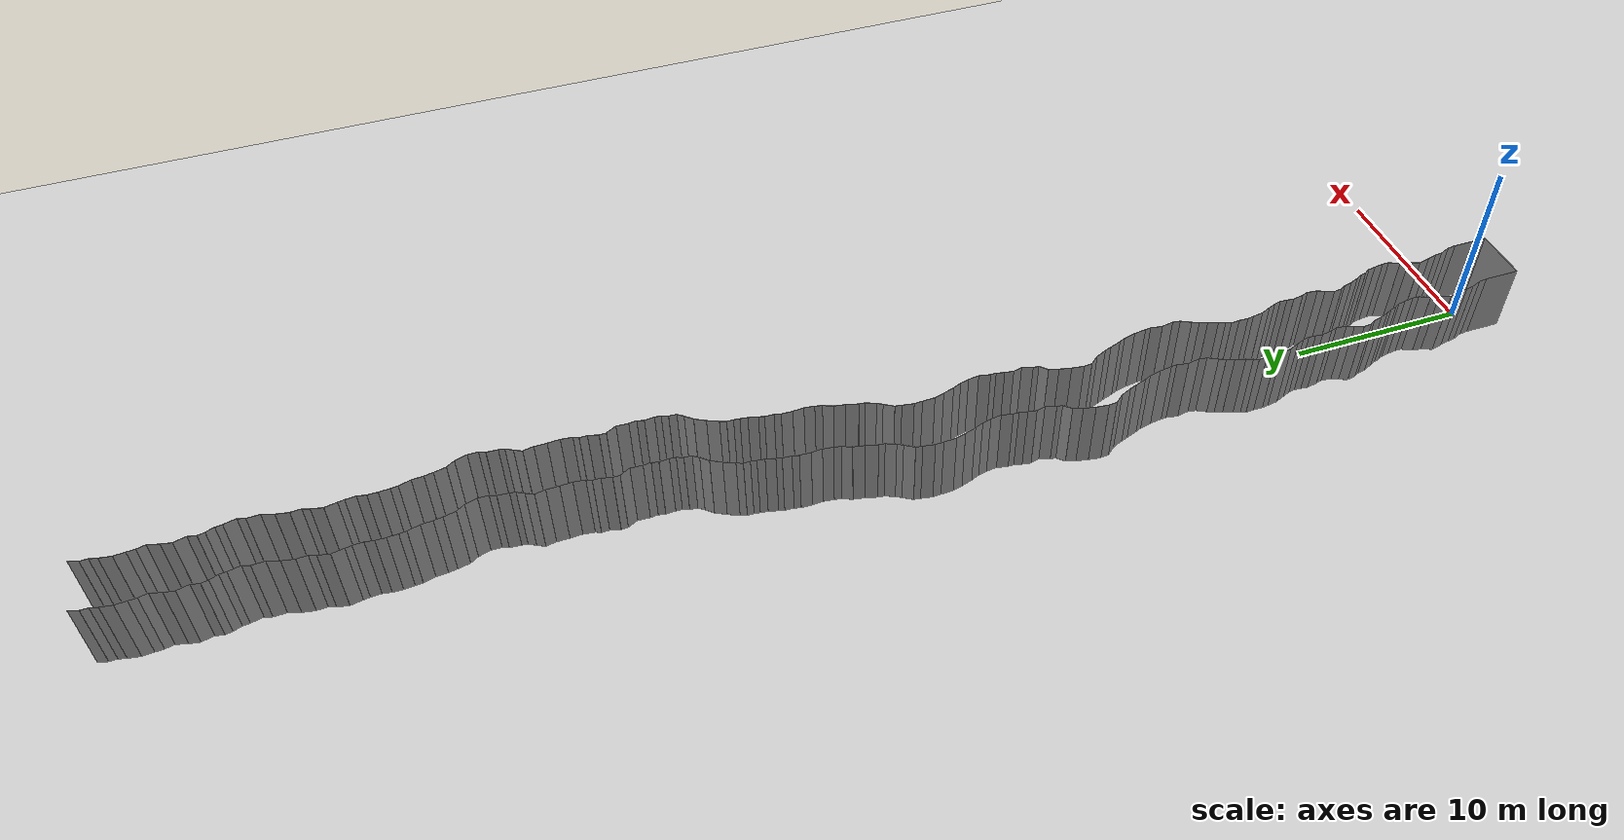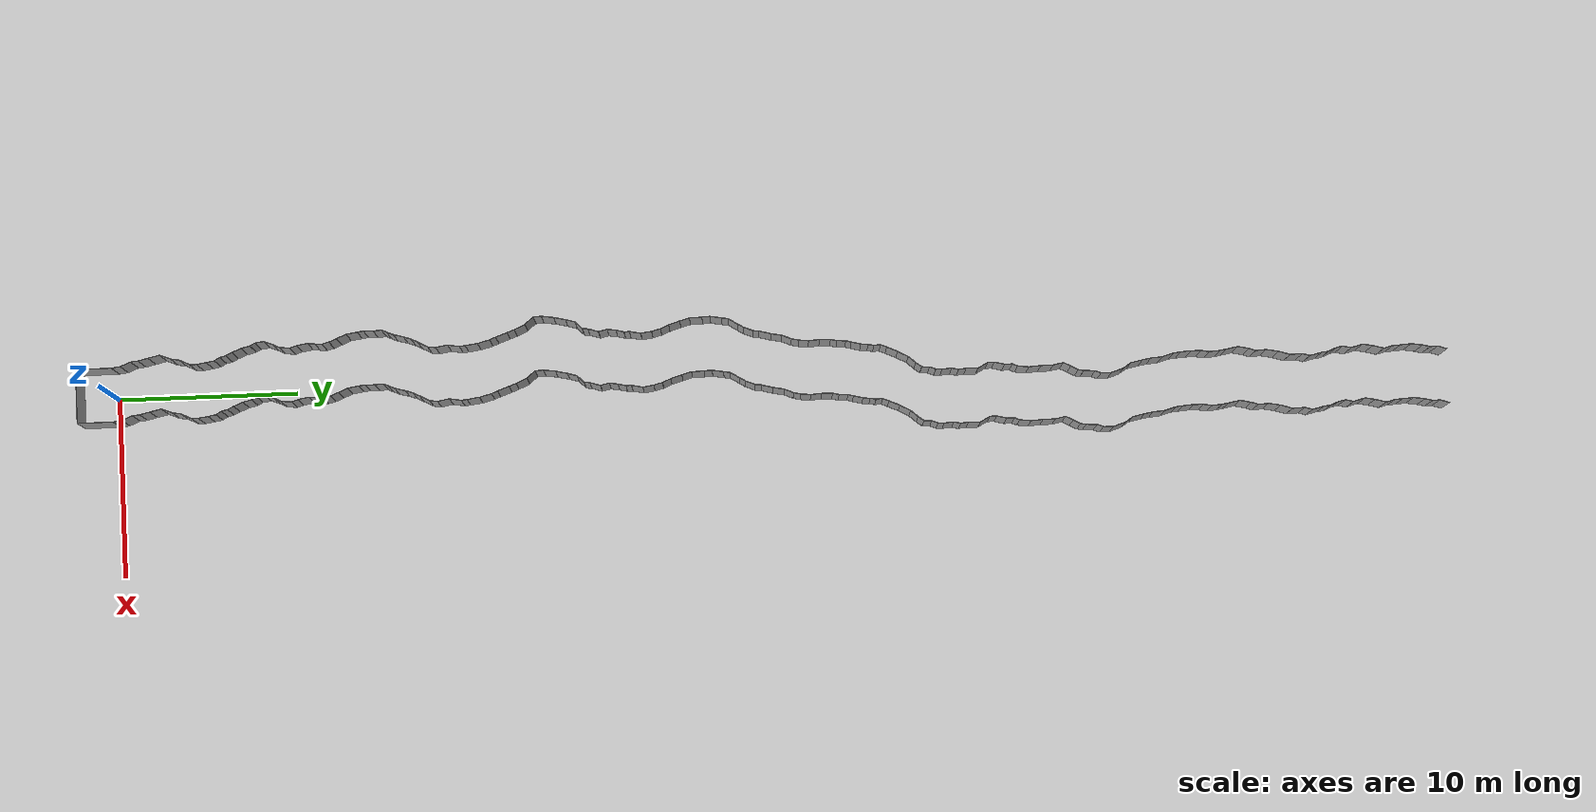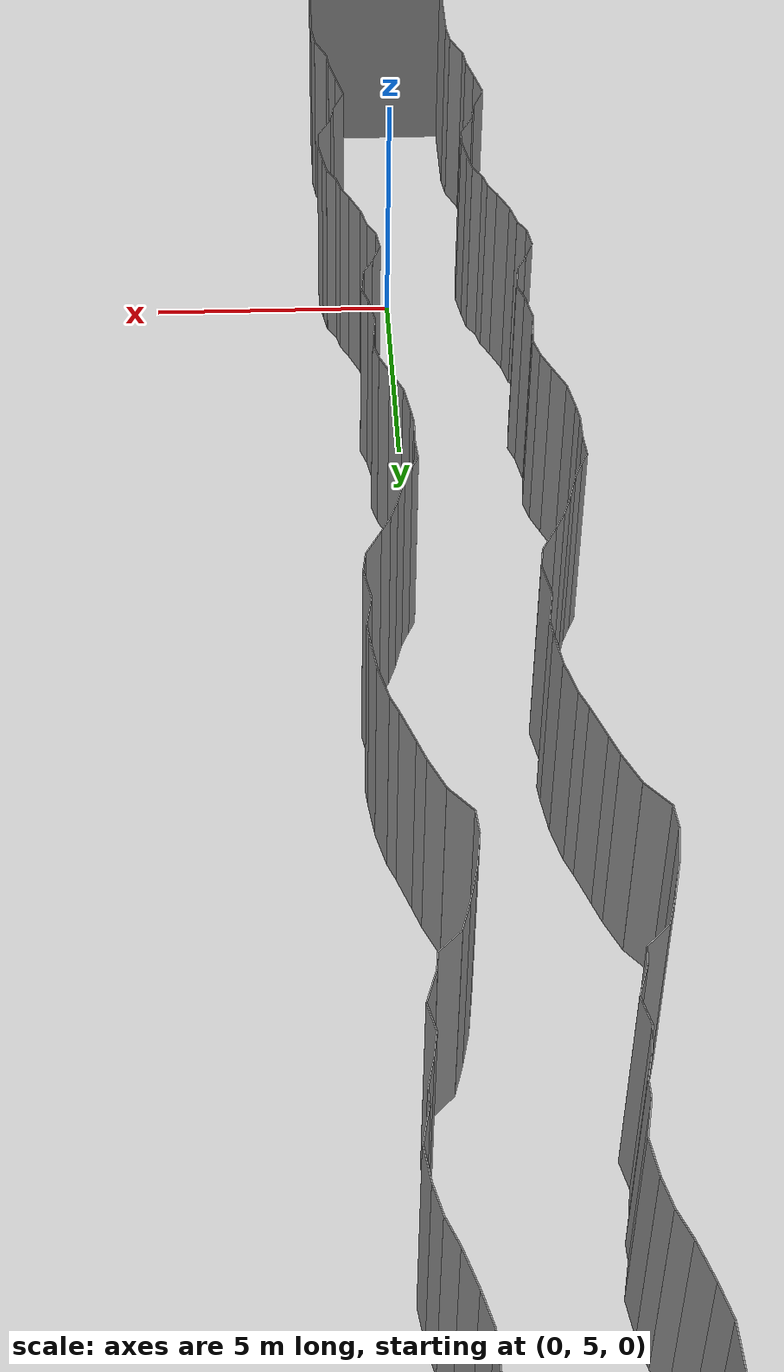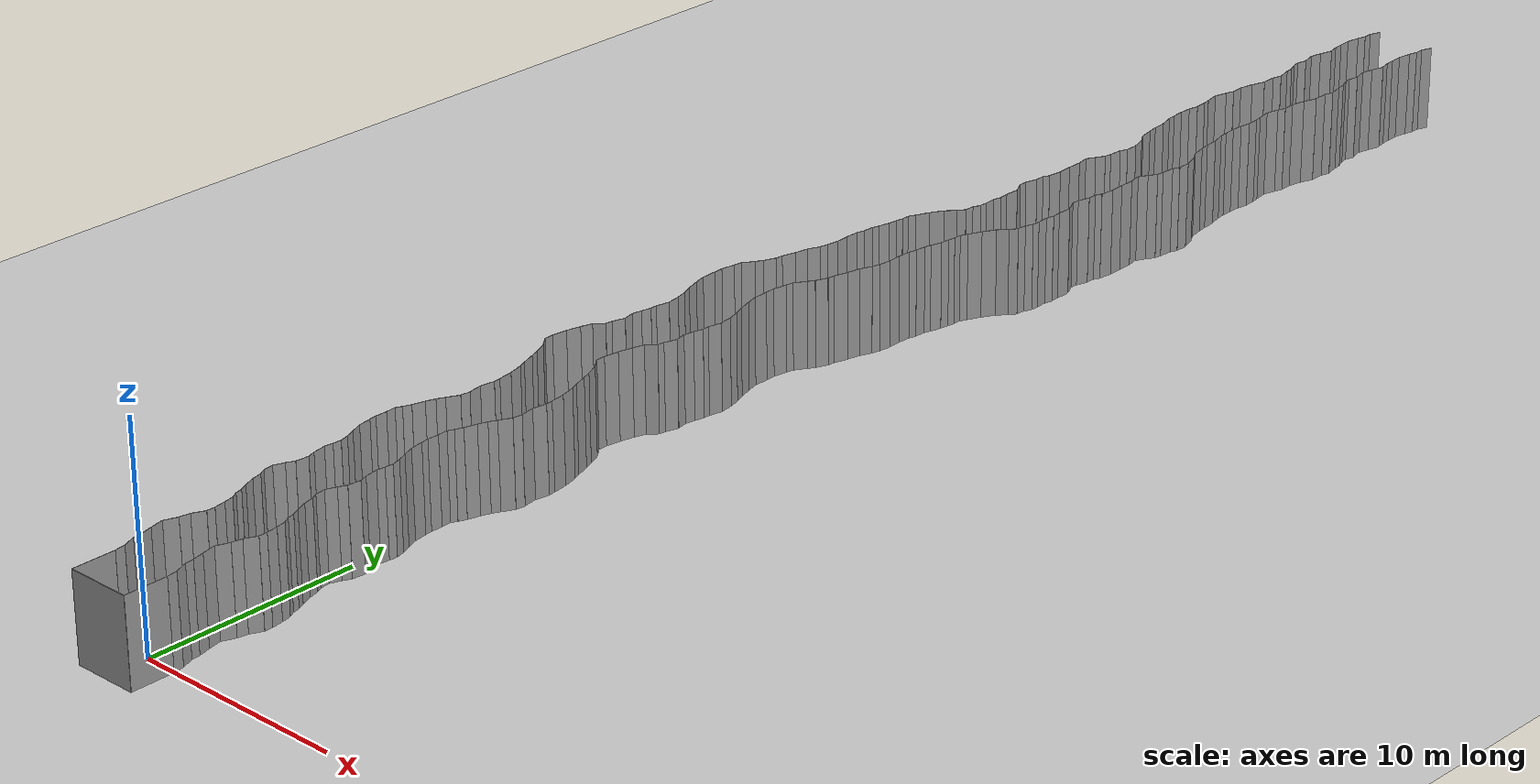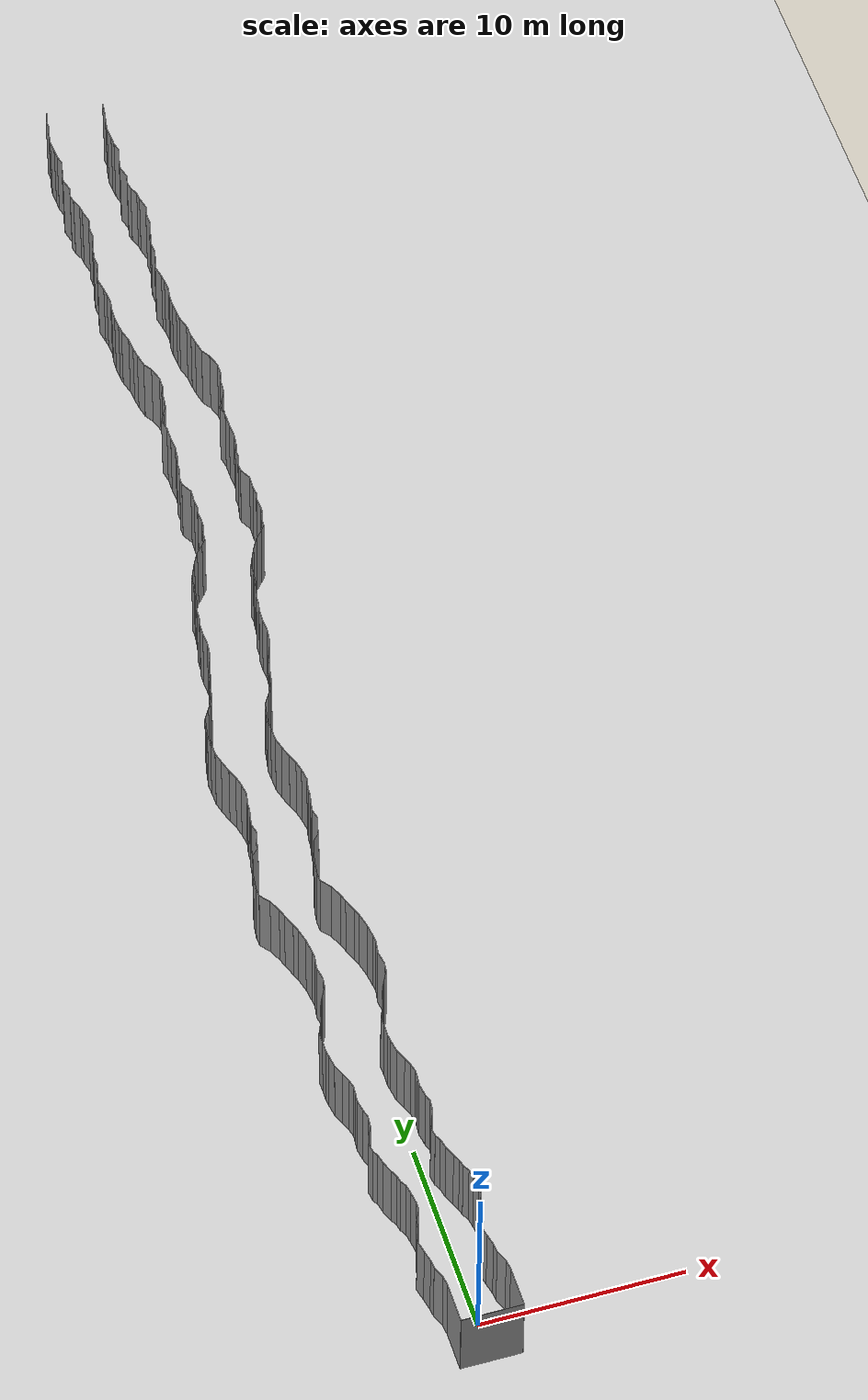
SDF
<sdf version="1.6">
 <world name="default">
  <light name="sun" type="directional">
   <pose>0 0 10 0 -0 0</pose>
   <diffuse>0.8 0.8 0.8 1</diffuse>
   <specular>0.2 0.2 0.2 1</specular>
   <attenuation>
    <range>1000</range>
    <constant>0.9</constant>
    <linear>0.01</linear>
    <quadratic>0.001</quadratic>
   </attenuation>
   <direction>-0.5 0.1 -0.9</direction>
  </light>
  <model name="ground_plane">
   <static>1</static>
   <link name="link">
    <collision name="collision">
     <geometry><plane><normal>0 0 1</normal><size>200 200</size></plane></geometry>
     <surface><friction><ode><mu>100</mu><mu2>50</mu2></ode></friction></surface>
    </collision>
    <visual name="visual">
     <cast_shadows>0</cast_shadows>
     <geometry><plane><normal>0 0 1</normal><size>200 200</size></plane></geometry>
     <material>
      <script><uri>file://media/materials/scripts/gazebo.material</uri><name>Gazebo/Grey</name></script>
     </material>
    </visual>
   </link>
   <pose>0 100 0 0 -0 0</pose>
  </model>
  <gravity>0 0 -9.8</gravity>
  <magnetic_field>6e-06 2.3e-05 -4.2e-05</magnetic_field>
  <atmosphere type="adiabatic"/>
  <physics default="0" name="default_physics" type="ode">
   <max_step_size>0.001</max_step_size>
   <real_time_factor>1</real_time_factor>
   <real_time_update_rate>1000</real_time_update_rate>
  </physics>
  <scene><ambient>0.4 0.4 0.4 1</ambient><background>0.7 0.7 0.7 1</background><shadows>1</shadows></scene>
  <spherical_coordinates>
   <surface_model>EARTH_WGS84</surface_model>
   <latitude_deg>0</latitude_deg>
   <longitude_deg>0</longitude_deg>
   <elevation>0</elevation>
   <heading_deg>0</heading_deg>
  </spherical_coordinates>
  <model name="wall_back">
   <static>1</static>
   <pose>0.0 -2 2 0.0 0 0.0</pose>
   <link name="link">
    <collision name="collision"><geometry><box><size>3 0.02 4</size></box></geometry></collision>
    <visual name="visual">
     <material>
      <script><name>Gazebo/Grey</name><uri>file://media/materials/scripts/gazebo.material</uri></script>
     </material>
     <geometry><box><size>3 0.02 4</size></box></geometry>
    </visual>
   </link>
  </model>
  <model name="wall_left">
   <static>1</static>
   <pose>1.5 -1 2 0 0 0.00</pose>
   <link name="link">
    <collision name="collision"><geometry><box><size>0.02 2 4</size></box></geometry></collision>
    <visual name="visual">
     <material>
      <script><name>Gazebo/Grey</name><uri>file://media/materials/scripts/gazebo.material</uri></script>
     </material>
     <geometry><box><size>0.02 2 4</size></box></geometry>
    </visual>
   </link>
  </model>
  <model name="wall_right">
   <static>1</static>
   <pose>-1.5 -1 2 0 0 0.00</pose>
   <link name="link">
    <collision name="collision"><geometry><box><size>0.02 2 4</size></box></geometry></collision>
    <visual name="visual">
     <material>
      <script><name>Gazebo/Grey</name><uri>file://media/materials/scripts/gazebo.material</uri></script>
     </material>
     <geometry><box><size>0.02 2 4</size></box></geometry>
    </visual>
   </link>
  </model>
  <model name="wall_0">
   <static>1</static>
   <pose>-1.5307311687963603 0.24682007867175873 2 0 0 0.12387091126973554</pose>
   <link name="link">
    <collision name="collision"><geometry><box><size>0.02 0.497451730206 4</size></box></geometry></collision>
    <visual name="visual">
     <material>
      <script><name>Gazebo/Grey</name><uri>file://media/materials/scripts/gazebo.material</uri></script>
     </material>
     <geometry><box><size>0.02 0.497451730206 4</size></box></geometry>
    </visual>
   </link>
  </model>
  <model name="wall_1">
   <static>1</static>
   <pose>1.4692688312036397 0.24682007867175873 2 0 0 0.12387091126973554</pose>
   <link name="link">
    <collision name="collision"><geometry><box><size>0.02 0.497451730206 4</size></box></geometry></collision>
    <visual name="visual">
     <material>
      <script><name>Gazebo/Grey</name><uri>file://media/materials/scripts/gazebo.material</uri></script>
     </material>
     <geometry><box><size>0.02 0.497451730206 4</size></box></geometry>
    </visual>
   </link>
  </model>
  <model name="wall_2">
   <static>1</static>
   <pose>-1.680255695739214 0.788827672844604 2 0 0 0.38260249823705095</pose>
   <link name="link">
    <collision name="collision"><geometry><box><size>0.02 0.63638834448 4</size></box></geometry></collision>
    <visual name="visual">
     <material>
      <script><name>Gazebo/Grey</name><uri>file://media/materials/scripts/gazebo.material</uri></script>
     </material>
     <geometry><box><size>0.02 0.63638834448 4</size></box></geometry>
    </visual>
   </link>
  </model>
  <model name="wall_3">
   <static>1</static>
   <pose>1.319744304260786 0.788827672844604 2 0 0 0.38260249823705095</pose>
   <link name="link">
    <collision name="collision"><geometry><box><size>0.02 0.63638834448 4</size></box></geometry></collision>
    <visual name="visual">
     <material>
      <script><name>Gazebo/Grey</name><uri>file://media/materials/scripts/gazebo.material</uri></script>
     </material>
     <geometry><box><size>0.02 0.63638834448 4</size></box></geometry>
    </visual>
   </link>
  </model>
  <model name="wall_4">
   <static>1</static>
   <pose>-1.8189245630661273 1.2884636229853923 2 0 0 0.09691073778679689</pose>
   <link name="link">
    <collision name="collision"><geometry><box><size>0.02 0.410824528439 4</size></box></geometry></collision>
    <visual name="visual">
     <material>
      <script><name>Gazebo/Grey</name><uri>file://media/materials/scripts/gazebo.material</uri></script>
     </material>
     <geometry><box><size>0.02 0.410824528439 4</size></box></geometry>
    </visual>
   </link>
  </model>
  <model name="wall_5">
   <static>1</static>
   <pose>1.1810754369338727 1.2884636229853923 2 0 0 0.09691073778679689</pose>
   <link name="link">
    <collision name="collision"><geometry><box><size>0.02 0.410824528439 4</size></box></geometry></collision>
    <visual name="visual">
     <material>
      <script><name>Gazebo/Grey</name><uri>file://media/materials/scripts/gazebo.material</uri></script>
     </material>
     <geometry><box><size>0.02 0.410824528439 4</size></box></geometry>
    </visual>
   </link>
  </model>
  <model name="wall_6">
   <static>1</static>
   <pose>-1.9046529150720921 1.7745180656748016 2 0 0 0.22971943522785104</pose>
   <link name="link">
    <collision name="collision"><geometry><box><size>0.02 0.578406572155 4</size></box></geometry></collision>
    <visual name="visual">
     <material>
      <script><name>Gazebo/Grey</name><uri>file://media/materials/scripts/gazebo.material</uri></script>
     </material>
     <geometry><box><size>0.02 0.578406572155 4</size></box></geometry>
    </visual>
   </link>
  </model>
  <model name="wall_7">
   <static>1</static>
   <pose>1.0953470849279079 1.7745180656748016 2 0 0 0.22971943522785104</pose>
   <link name="link">
    <collision name="collision"><geometry><box><size>0.02 0.578406572155 4</size></box></geometry></collision>
    <visual name="visual">
     <material>
      <script><name>Gazebo/Grey</name><uri>file://media/materials/scripts/gazebo.material</uri></script>
     </material>
     <geometry><box><size>0.02 0.578406572155 4</size></box></geometry>
    </visual>
   </link>
  </model>
  <model name="wall_8">
   <static>1</static>
   <pose>-2.0421624320793557 2.3812499141331216 2 0 0 0.21692869439451723</pose>
   <link name="link">
    <collision name="collision"><geometry><box><size>0.02 0.665857315215 4</size></box></geometry></collision>
    <visual name="visual">
     <material>
      <script><name>Gazebo/Grey</name><uri>file://media/materials/scripts/gazebo.material</uri></script>
     </material>
     <geometry><box><size>0.02 0.665857315215 4</size></box></geometry>
    </visual>
   </link>
  </model>
  <model name="wall_9">
   <static>1</static>
   <pose>0.9578375679206443 2.3812499141331216 2 0 0 0.21692869439451723</pose>
   <link name="link">
    <collision name="collision"><geometry><box><size>0.02 0.665857315215 4</size></box></geometry></collision>
    <visual name="visual">
     <material>
      <script><name>Gazebo/Grey</name><uri>file://media/materials/scripts/gazebo.material</uri></script>
     </material>
     <geometry><box><size>0.02 0.665857315215 4</size></box></geometry>
    </visual>
   </link>
  </model>
  <model name="wall_10">
   <static>1</static>
   <pose>-1.9958734557599482 3.0080293722450535 2 0 0 -0.37272113188731054</pose>
   <link name="link">
    <collision name="collision"><geometry><box><size>0.02 0.647784166357 4</size></box></geometry></collision>
    <visual name="visual">
     <material>
      <script><name>Gazebo/Grey</name><uri>file://media/materials/scripts/gazebo.material</uri></script>
     </material>
     <geometry><box><size>0.02 0.647784166357 4</size></box></geometry>
    </visual>
   </link>
  </model>
  <model name="wall_11">
   <static>1</static>
   <pose>1.0041265442400518 3.0080293722450535 2 0 0 -0.37272113188731054</pose>
   <link name="link">
    <collision name="collision"><geometry><box><size>0.02 0.647784166357 4</size></box></geometry></collision>
    <visual name="visual">
     <material>
      <script><name>Gazebo/Grey</name><uri>file://media/materials/scripts/gazebo.material</uri></script>
     </material>
     <geometry><box><size>0.02 0.647784166357 4</size></box></geometry>
    </visual>
   </link>
  </model>
  <model name="wall_12">
   <static>1</static>
   <pose>-1.8371151136807784 3.5522359761309676 2 0 0 -0.16670145723548743</pose>
   <link name="link">
    <collision name="collision"><geometry><box><size>0.02 0.491925306932 4</size></box></geometry></collision>
    <visual name="visual">
     <material>
      <script><name>Gazebo/Grey</name><uri>file://media/materials/scripts/gazebo.material</uri></script>
     </material>
     <geometry><box><size>0.02 0.491925306932 4</size></box></geometry>
    </visual>
   </link>
  </model>
  <model name="wall_13">
   <static>1</static>
   <pose>1.1628848863192216 3.5522359761309676 2 0 0 -0.16670145723548743</pose>
   <link name="link">
    <collision name="collision"><geometry><box><size>0.02 0.491925306932 4</size></box></geometry></collision>
    <visual name="visual">
     <material>
      <script><name>Gazebo/Grey</name><uri>file://media/materials/scripts/gazebo.material</uri></script>
     </material>
     <geometry><box><size>0.02 0.491925306932 4</size></box></geometry>
    </visual>
   </link>
  </model>
  <model name="wall_14">
   <static>1</static>
   <pose>-1.6612287422368008 4.074180786566131 2 0 0 -0.45032510420682703</pose>
   <link name="link">
    <collision name="collision"><geometry><box><size>0.02 0.620659940553 4</size></box></geometry></collision>
    <visual name="visual">
     <material>
      <script><name>Gazebo/Grey</name><uri>file://media/materials/scripts/gazebo.material</uri></script>
     </material>
     <geometry><box><size>0.02 0.620659940553 4</size></box></geometry>
    </visual>
   </link>
  </model>
  <model name="wall_15">
   <static>1</static>
   <pose>1.3387712577631992 4.074180786566131 2 0 0 -0.45032510420682703</pose>
   <link name="link">
    <collision name="collision"><geometry><box><size>0.02 0.620659940553 4</size></box></geometry></collision>
    <visual name="visual">
     <material>
      <script><name>Gazebo/Grey</name><uri>file://media/materials/scripts/gazebo.material</uri></script>
     </material>
     <geometry><box><size>0.02 0.620659940553 4</size></box></geometry>
    </visual>
   </link>
  </model>
  <model name="wall_16">
   <static>1</static>
   <pose>-1.5216878284495352 4.546500633476221 2 0 0 -0.023150788291668885</pose>
   <link name="link">
    <collision name="collision"><geometry><box><size>0.02 0.385959469921 4</size></box></geometry></collision>
    <visual name="visual">
     <material>
      <script><name>Gazebo/Grey</name><uri>file://media/materials/scripts/gazebo.material</uri></script>
     </material>
     <geometry><box><size>0.02 0.385959469921 4</size></box></geometry>
    </visual>
   </link>
  </model>
  <model name="wall_17">
   <static>1</static>
   <pose>1.4783121715504648 4.546500633476221 2 0 0 -0.023150788291668885</pose>
   <link name="link">
    <collision name="collision"><geometry><box><size>0.02 0.385959469921 4</size></box></geometry></collision>
    <visual name="visual">
     <material>
      <script><name>Gazebo/Grey</name><uri>file://media/materials/scripts/gazebo.material</uri></script>
     </material>
     <geometry><box><size>0.02 0.385959469921 4</size></box></geometry>
    </visual>
   </link>
  </model>
  <model name="wall_18">
   <static>1</static>
   <pose>-1.5572613715143004 5.01056779444807 2 0 0 0.14661643700674581</pose>
   <link name="link">
    <collision name="collision"><geometry><box><size>0.02 0.548159451793 4</size></box></geometry></collision>
    <visual name="visual">
     <material>
      <script><name>Gazebo/Grey</name><uri>file://media/materials/scripts/gazebo.material</uri></script>
     </material>
     <geometry><box><size>0.02 0.548159451793 4</size></box></geometry>
    </visual>
   </link>
  </model>
  <model name="wall_19">
   <static>1</static>
   <pose>1.4427386284856996 5.01056779444807 2 0 0 0.14661643700674581</pose>
   <link name="link">
    <collision name="collision"><geometry><box><size>0.02 0.548159451793 4</size></box></geometry></collision>
    <visual name="visual">
     <material>
      <script><name>Gazebo/Grey</name><uri>file://media/materials/scripts/gazebo.material</uri></script>
     </material>
     <geometry><box><size>0.02 0.548159451793 4</size></box></geometry>
    </visual>
   </link>
  </model>
  <model name="wall_20">
   <static>1</static>
   <pose>-1.6368601609359468 5.505053012077374 2 0 0 0.1752973904942411</pose>
   <link name="link">
    <collision name="collision"><geometry><box><size>0.02 0.453644387128 4</size></box></geometry></collision>
    <visual name="visual">
     <material>
      <script><name>Gazebo/Grey</name><uri>file://media/materials/scripts/gazebo.material</uri></script>
     </material>
     <geometry><box><size>0.02 0.453644387128 4</size></box></geometry>
    </visual>
   </link>
  </model>
  <model name="wall_21">
   <static>1</static>
   <pose>1.3631398390640532 5.505053012077374 2 0 0 0.1752973904942411</pose>
   <link name="link">
    <collision name="collision"><geometry><box><size>0.02 0.453644387128 4</size></box></geometry></collision>
    <visual name="visual">
     <material>
      <script><name>Gazebo/Grey</name><uri>file://media/materials/scripts/gazebo.material</uri></script>
     </material>
     <geometry><box><size>0.02 0.453644387128 4</size></box></geometry>
    </visual>
   </link>
  </model>
  <model name="wall_22">
   <static>1</static>
   <pose>-1.7660356316071537 5.885742513176066 2 0 0 0.5177408707553595</pose>
   <link name="link">
    <collision name="collision"><geometry><box><size>0.02 0.36215047259 4</size></box></geometry></collision>
    <visual name="visual">
     <material>
      <script><name>Gazebo/Grey</name><uri>file://media/materials/scripts/gazebo.material</uri></script>
     </material>
     <geometry><box><size>0.02 0.36215047259 4</size></box></geometry>
    </visual>
   </link>
  </model>
  <model name="wall_23">
   <static>1</static>
   <pose>1.2339643683928463 5.885742513176066 2 0 0 0.5177408707553595</pose>
   <link name="link">
    <collision name="collision"><geometry><box><size>0.02 0.36215047259 4</size></box></geometry></collision>
    <visual name="visual">
     <material>
      <script><name>Gazebo/Grey</name><uri>file://media/materials/scripts/gazebo.material</uri></script>
     </material>
     <geometry><box><size>0.02 0.36215047259 4</size></box></geometry>
    </visual>
   </link>
  </model>
  <model name="wall_24">
   <static>1</static>
   <pose>-1.894587063273864 6.20996375331709 2 0 0 0.22920815441649556</pose>
   <link name="link">
    <collision name="collision"><geometry><box><size>0.02 0.342718896747 4</size></box></geometry></collision>
    <visual name="visual">
     <material>
      <script><name>Gazebo/Grey</name><uri>file://media/materials/scripts/gazebo.material</uri></script>
     </material>
     <geometry><box><size>0.02 0.342718896747 4</size></box></geometry>
    </visual>
   </link>
  </model>
  <model name="wall_25">
   <static>1</static>
   <pose>1.105412936726136 6.20996375331709 2 0 0 0.22920815441649556</pose>
   <link name="link">
    <collision name="collision"><geometry><box><size>0.02 0.342718896747 4</size></box></geometry></collision>
    <visual name="visual">
     <material>
      <script><name>Gazebo/Grey</name><uri>file://media/materials/scripts/gazebo.material</uri></script>
     </material>
     <geometry><box><size>0.02 0.342718896747 4</size></box></geometry>
    </visual>
   </link>
  </model>
  <model name="wall_26">
   <static>1</static>
   <pose>-2.017375926076146 6.551261584629678 2 0 0 0.44814084864739206</pose>
   <link name="link">
    <collision name="collision"><geometry><box><size>0.02 0.387060632929 4</size></box></geometry></collision>
    <visual name="visual">
     <material>
      <script><name>Gazebo/Grey</name><uri>file://media/materials/scripts/gazebo.material</uri></script>
     </material>
     <geometry><box><size>0.02 0.387060632929 4</size></box></geometry>
    </visual>
   </link>
  </model>
  <model name="wall_27">
   <static>1</static>
   <pose>0.9826240739238541 6.551261584629678 2 0 0 0.44814084864739206</pose>
   <link name="link">
    <collision name="collision"><geometry><box><size>0.02 0.387060632929 4</size></box></geometry></collision>
    <visual name="visual">
     <material>
      <script><name>Gazebo/Grey</name><uri>file://media/materials/scripts/gazebo.material</uri></script>
     </material>
     <geometry><box><size>0.02 0.387060632929 4</size></box></geometry>
    </visual>
   </link>
  </model>
  <model name="wall_28">
   <static>1</static>
   <pose>-2.206541215022592 6.983666569921456 2 0 0 0.38755839696092276</pose>
   <link name="link">
    <collision name="collision"><geometry><box><size>0.02 0.557302525421 4</size></box></geometry></collision>
    <visual name="visual">
     <material>
      <script><name>Gazebo/Grey</name><uri>file://media/materials/scripts/gazebo.material</uri></script>
     </material>
     <geometry><box><size>0.02 0.557302525421 4</size></box></geometry>
    </visual>
   </link>
  </model>
  <model name="wall_29">
   <static>1</static>
   <pose>0.7934587849774082 6.983666569921456 2 0 0 0.38755839696092276</pose>
   <link name="link">
    <collision name="collision"><geometry><box><size>0.02 0.557302525421 4</size></box></geometry></collision>
    <visual name="visual">
     <material>
      <script><name>Gazebo/Grey</name><uri>file://media/materials/scripts/gazebo.material</uri></script>
     </material>
     <geometry><box><size>0.02 0.557302525421 4</size></box></geometry>
    </visual>
   </link>
  </model>
  <model name="wall_30">
   <static>1</static>
   <pose>-2.367312638487156 7.487475205102649 2 0 0 0.22189786602542222</pose>
   <link name="link">
    <collision name="collision"><geometry><box><size>0.02 0.504004755475 4</size></box></geometry></collision>
    <visual name="visual">
     <material>
      <script><name>Gazebo/Grey</name><uri>file://media/materials/scripts/gazebo.material</uri></script>
     </material>
     <geometry><box><size>0.02 0.504004755475 4</size></box></geometry>
    </visual>
   </link>
  </model>
  <model name="wall_31">
   <static>1</static>
   <pose>0.6326873615128439 7.487475205102649 2 0 0 0.22189786602542222</pose>
   <link name="link">
    <collision name="collision"><geometry><box><size>0.02 0.504004755475 4</size></box></geometry></collision>
    <visual name="visual">
     <material>
      <script><name>Gazebo/Grey</name><uri>file://media/materials/scripts/gazebo.material</uri></script>
     </material>
     <geometry><box><size>0.02 0.504004755475 4</size></box></geometry>
    </visual>
   </link>
  </model>
  <model name="wall_32">
   <static>1</static>
   <pose>-2.5020238359366775 7.877625891850845 2 0 0 0.5021530593760419</pose>
   <link name="link">
    <collision name="collision"><geometry><box><size>0.02 0.329307636341 4</size></box></geometry></collision>
    <visual name="visual">
     <material>
      <script><name>Gazebo/Grey</name><uri>file://media/materials/scripts/gazebo.material</uri></script>
     </material>
     <geometry><box><size>0.02 0.329307636341 4</size></box></geometry>
    </visual>
   </link>
  </model>
  <model name="wall_33">
   <static>1</static>
   <pose>0.49797616406332246 7.877625891850845 2 0 0 0.5021530593760419</pose>
   <link name="link">
    <collision name="collision"><geometry><box><size>0.02 0.329307636341 4</size></box></geometry></collision>
    <visual name="visual">
     <material>
      <script><name>Gazebo/Grey</name><uri>file://media/materials/scripts/gazebo.material</uri></script>
     </material>
     <geometry><box><size>0.02 0.329307636341 4</size></box></geometry>
    </visual>
   </link>
  </model>
  <model name="wall_34">
   <static>1</static>
   <pose>-2.612442737876426 8.264369004179834 2 0 0 0.12787375578342494</pose>
   <link name="link">
    <collision name="collision"><geometry><box><size>0.02 0.488823279136 4</size></box></geometry></collision>
    <visual name="visual">
     <material>
      <script><name>Gazebo/Grey</name><uri>file://media/materials/scripts/gazebo.material</uri></script>
     </material>
     <geometry><box><size>0.02 0.488823279136 4</size></box></geometry>
    </visual>
   </link>
  </model>
  <model name="wall_35">
   <static>1</static>
   <pose>0.3875572621235741 8.264369004179834 2 0 0 0.12787375578342494</pose>
   <link name="link">
    <collision name="collision"><geometry><box><size>0.02 0.488823279136 4</size></box></geometry></collision>
    <visual name="visual">
     <material>
      <script><name>Gazebo/Grey</name><uri>file://media/materials/scripts/gazebo.material</uri></script>
     </material>
     <geometry><box><size>0.02 0.488823279136 4</size></box></geometry>
    </visual>
   </link>
  </model>
  <model name="wall_36">
   <static>1</static>
   <pose>-2.5546231025190207 8.750861470290321 2 0 0 -0.3496150232994657</pose>
   <link name="link">
    <collision name="collision"><geometry><box><size>0.02 0.519585246228 4</size></box></geometry></collision>
    <visual name="visual">
     <material>
      <script><name>Gazebo/Grey</name><uri>file://media/materials/scripts/gazebo.material</uri></script>
     </material>
     <geometry><box><size>0.02 0.519585246228 4</size></box></geometry>
    </visual>
   </link>
  </model>
  <model name="wall_37">
   <static>1</static>
   <pose>0.4453768974809793 8.750861470290321 2 0 0 -0.3496150232994657</pose>
   <link name="link">
    <collision name="collision"><geometry><box><size>0.02 0.519585246228 4</size></box></geometry></collision>
    <visual name="visual">
     <material>
      <script><name>Gazebo/Grey</name><uri>file://media/materials/scripts/gazebo.material</uri></script>
     </material>
     <geometry><box><size>0.02 0.519585246228 4</size></box></geometry>
    </visual>
   </link>
  </model>
  <model name="wall_38">
   <static>1</static>
   <pose>-2.374421227251 9.177686558201325 2 0 0 -0.4629432529449416</pose>
   <link name="link">
    <collision name="collision"><geometry><box><size>0.02 0.408494777323 4</size></box></geometry></collision>
    <visual name="visual">
     <material>
      <script><name>Gazebo/Grey</name><uri>file://media/materials/scripts/gazebo.material</uri></script>
     </material>
     <geometry><box><size>0.02 0.408494777323 4</size></box></geometry>
    </visual>
   </link>
  </model>
  <model name="wall_39">
   <static>1</static>
   <pose>0.6255787727489999 9.177686558201325 2 0 0 -0.4629432529449416</pose>
   <link name="link">
    <collision name="collision"><geometry><box><size>0.02 0.408494777323 4</size></box></geometry></collision>
    <visual name="visual">
     <material>
      <script><name>Gazebo/Grey</name><uri>file://media/materials/scripts/gazebo.material</uri></script>
     </material>
     <geometry><box><size>0.02 0.408494777323 4</size></box></geometry>
    </visual>
   </link>
  </model>
  <model name="wall_40">
   <static>1</static>
   <pose>-2.2512681147087266 9.656876612745306 2 0 0 -0.10732937084118686</pose>
   <link name="link">
    <collision name="collision"><geometry><box><size>0.02 0.596314040532 4</size></box></geometry></collision>
    <visual name="visual">
     <material>
      <script><name>Gazebo/Grey</name><uri>file://media/materials/scripts/gazebo.material</uri></script>
     </material>
     <geometry><box><size>0.02 0.596314040532 4</size></box></geometry>
    </visual>
   </link>
  </model>
  <model name="wall_41">
   <static>1</static>
   <pose>0.7487318852912734 9.656876612745306 2 0 0 -0.10732937084118686</pose>
   <link name="link">
    <collision name="collision"><geometry><box><size>0.02 0.596314040532 4</size></box></geometry></collision>
    <visual name="visual">
     <material>
      <script><name>Gazebo/Grey</name><uri>file://media/materials/scripts/gazebo.material</uri></script>
     </material>
     <geometry><box><size>0.02 0.596314040532 4</size></box></geometry>
    </visual>
   </link>
  </model>
  <model name="wall_42">
   <static>1</static>
   <pose>-2.279305843786663 10.13536134345769 2 0 0 0.31826703435486514</pose>
   <link name="link">
    <collision name="collision"><geometry><box><size>0.02 0.383338360484 4</size></box></geometry></collision>
    <visual name="visual">
     <material>
      <script><name>Gazebo/Grey</name><uri>file://media/materials/scripts/gazebo.material</uri></script>
     </material>
     <geometry><box><size>0.02 0.383338360484 4</size></box></geometry>
    </visual>
   </link>
  </model>
  <model name="wall_43">
   <static>1</static>
   <pose>0.7206941562133369 10.13536134345769 2 0 0 0.31826703435486514</pose>
   <link name="link">
    <collision name="collision"><geometry><box><size>0.02 0.383338360484 4</size></box></geometry></collision>
    <visual name="visual">
     <material>
      <script><name>Gazebo/Grey</name><uri>file://media/materials/scripts/gazebo.material</uri></script>
     </material>
     <geometry><box><size>0.02 0.383338360484 4</size></box></geometry>
    </visual>
   </link>
  </model>
  <model name="wall_44">
   <static>1</static>
   <pose>-2.3909150131062504 10.62686349971056 2 0 0 0.16532278568679626</pose>
   <link name="link">
    <collision name="collision"><geometry><box><size>0.02 0.627472954205 4</size></box></geometry></collision>
    <visual name="visual">
     <material>
      <script><name>Gazebo/Grey</name><uri>file://media/materials/scripts/gazebo.material</uri></script>
     </material>
     <geometry><box><size>0.02 0.627472954205 4</size></box></geometry>
    </visual>
   </link>
  </model>
  <model name="wall_45">
   <static>1</static>
   <pose>0.6090849868937496 10.62686349971056 2 0 0 0.16532278568679626</pose>
   <link name="link">
    <collision name="collision"><geometry><box><size>0.02 0.627472954205 4</size></box></geometry></collision>
    <visual name="visual">
     <material>
      <script><name>Gazebo/Grey</name><uri>file://media/materials/scripts/gazebo.material</uri></script>
     </material>
     <geometry><box><size>0.02 0.627472954205 4</size></box></geometry>
    </visual>
   </link>
  </model>
  <model name="wall_46">
   <static>1</static>
   <pose>-2.420412665573124 11.136746123564082 2 0 0 -0.10999117134003332</pose>
   <link name="link">
    <collision name="collision"><geometry><box><size>0.02 0.403284730551 4</size></box></geometry></collision>
    <visual name="visual">
     <material>
      <script><name>Gazebo/Grey</name><uri>file://media/materials/scripts/gazebo.material</uri></script>
     </material>
     <geometry><box><size>0.02 0.403284730551 4</size></box></geometry>
    </visual>
   </link>
  </model>
  <model name="wall_47">
   <static>1</static>
   <pose>0.579587334426876 11.136746123564082 2 0 0 -0.10999117134003332</pose>
   <link name="link">
    <collision name="collision"><geometry><box><size>0.02 0.403284730551 4</size></box></geometry></collision>
    <visual name="visual">
     <material>
      <script><name>Gazebo/Grey</name><uri>file://media/materials/scripts/gazebo.material</uri></script>
     </material>
     <geometry><box><size>0.02 0.403284730551 4</size></box></geometry>
    </visual>
   </link>
  </model>
  <model name="wall_48">
   <static>1</static>
   <pose>-2.3829932997251992 11.53124501559094 2 0 0 -0.0785968751931339</pose>
   <link name="link">
    <collision name="collision"><geometry><box><size>0.02 0.389352062209 4</size></box></geometry></collision>
    <visual name="visual">
     <material>
      <script><name>Gazebo/Grey</name><uri>file://media/materials/scripts/gazebo.material</uri></script>
     </material>
     <geometry><box><size>0.02 0.389352062209 4</size></box></geometry>
    </visual>
   </link>
  </model>
  <model name="wall_49">
   <static>1</static>
   <pose>0.6170067002748008 11.53124501559094 2 0 0 -0.0785968751931339</pose>
   <link name="link">
    <collision name="collision"><geometry><box><size>0.02 0.389352062209 4</size></box></geometry></collision>
    <visual name="visual">
     <material>
      <script><name>Gazebo/Grey</name><uri>file://media/materials/scripts/gazebo.material</uri></script>
     </material>
     <geometry><box><size>0.02 0.389352062209 4</size></box></geometry>
    </visual>
   </link>
  </model>
  <model name="wall_50">
   <static>1</static>
   <pose>-2.417286680858652 11.926932043225607 2 0 0 0.24112629132991498</pose>
   <link name="link">
    <collision name="collision"><geometry><box><size>0.02 0.415236934701 4</size></box></geometry></collision>
    <visual name="visual">
     <material>
      <script><name>Gazebo/Grey</name><uri>file://media/materials/scripts/gazebo.material</uri></script>
     </material>
     <geometry><box><size>0.02 0.415236934701 4</size></box></geometry>
    </visual>
   </link>
  </model>
  <model name="wall_51">
   <static>1</static>
   <pose>0.582713319141348 11.926932043225607 2 0 0 0.24112629132991498</pose>
   <link name="link">
    <collision name="collision"><geometry><box><size>0.02 0.415236934701 4</size></box></geometry></collision>
    <visual name="visual">
     <material>
      <script><name>Gazebo/Grey</name><uri>file://media/materials/scripts/gazebo.material</uri></script>
     </material>
     <geometry><box><size>0.02 0.415236934701 4</size></box></geometry>
    </visual>
   </link>
  </model>
  <model name="wall_52">
   <static>1</static>
   <pose>-2.5535793469881813 12.344934107226788 2 0 0 0.38113597257273385</pose>
   <link name="link">
    <collision name="collision"><geometry><box><size>0.02 0.466235993729 4</size></box></geometry></collision>
    <visual name="visual">
     <material>
      <script><name>Gazebo/Grey</name><uri>file://media/materials/scripts/gazebo.material</uri></script>
     </material>
     <geometry><box><size>0.02 0.466235993729 4</size></box></geometry>
    </visual>
   </link>
  </model>
  <model name="wall_53">
   <static>1</static>
   <pose>0.44642065301181866 12.344934107226788 2 0 0 0.38113597257273385</pose>
   <link name="link">
    <collision name="collision"><geometry><box><size>0.02 0.466235993729 4</size></box></geometry></collision>
    <visual name="visual">
     <material>
      <script><name>Gazebo/Grey</name><uri>file://media/materials/scripts/gazebo.material</uri></script>
     </material>
     <geometry><box><size>0.02 0.466235993729 4</size></box></geometry>
    </visual>
   </link>
  </model>
  <model name="wall_54">
   <static>1</static>
   <pose>-2.752241674904807 12.83078565006214 2 0 0 0.39375542551548837</pose>
   <link name="link">
    <collision name="collision"><geometry><box><size>0.02 0.583581656265 4</size></box></geometry></collision>
    <visual name="visual">
     <material>
      <script><name>Gazebo/Grey</name><uri>file://media/materials/scripts/gazebo.material</uri></script>
     </material>
     <geometry><box><size>0.02 0.583581656265 4</size></box></geometry>
    </visual>
   </link>
  </model>
  <model name="wall_55">
   <static>1</static>
   <pose>0.24775832509519313 12.83078565006214 2 0 0 0.39375542551548837</pose>
   <link name="link">
    <collision name="collision"><geometry><box><size>0.02 0.583581656265 4</size></box></geometry></collision>
    <visual name="visual">
     <material>
      <script><name>Gazebo/Grey</name><uri>file://media/materials/scripts/gazebo.material</uri></script>
     </material>
     <geometry><box><size>0.02 0.583581656265 4</size></box></geometry>
    </visual>
   </link>
  </model>
  <model name="wall_56">
   <static>1</static>
   <pose>-2.912442377954267 13.410218648460438 2 0 0 0.15442803563107685</pose>
   <link name="link">
    <collision name="collision"><geometry><box><size>0.02 0.627409439883 4</size></box></geometry></collision>
    <visual name="visual">
     <material>
      <script><name>Gazebo/Grey</name><uri>file://media/materials/scripts/gazebo.material</uri></script>
     </material>
     <geometry><box><size>0.02 0.627409439883 4</size></box></geometry>
    </visual>
   </link>
  </model>
  <model name="wall_57">
   <static>1</static>
   <pose>0.08755762204573303 13.410218648460438 2 0 0 0.15442803563107685</pose>
   <link name="link">
    <collision name="collision"><geometry><box><size>0.02 0.627409439883 4</size></box></geometry></collision>
    <visual name="visual">
     <material>
      <script><name>Gazebo/Grey</name><uri>file://media/materials/scripts/gazebo.material</uri></script>
     </material>
     <geometry><box><size>0.02 0.627409439883 4</size></box></geometry>
    </visual>
   </link>
  </model>
  <model name="wall_58">
   <static>1</static>
   <pose>-2.9828431748856477 13.895429289360354 2 0 0 0.12572250244429348</pose>
   <link name="link">
    <collision name="collision"><geometry><box><size>0.02 0.353266437122 4</size></box></geometry></collision>
    <visual name="visual">
     <material>
      <script><name>Gazebo/Grey</name><uri>file://media/materials/scripts/gazebo.material</uri></script>
     </material>
     <geometry><box><size>0.02 0.353266437122 4</size></box></geometry>
    </visual>
   </link>
  </model>
  <model name="wall_59">
   <static>1</static>
   <pose>0.017156825114352348 13.895429289360354 2 0 0 0.12572250244429348</pose>
   <link name="link">
    <collision name="collision"><geometry><box><size>0.02 0.353266437122 4</size></box></geometry></collision>
    <visual name="visual">
     <material>
      <script><name>Gazebo/Grey</name><uri>file://media/materials/scripts/gazebo.material</uri></script>
     </material>
     <geometry><box><size>0.02 0.353266437122 4</size></box></geometry>
    </visual>
   </link>
  </model>
  <model name="wall_60">
   <static>1</static>
   <pose>-2.9979367667694157 14.339573363887226 2 0 0 -0.026228992002993258</pose>
   <link name="link">
    <collision name="collision"><geometry><box><size>0.02 0.537994976085 4</size></box></geometry></collision>
    <visual name="visual">
     <material>
      <script><name>Gazebo/Grey</name><uri>file://media/materials/scripts/gazebo.material</uri></script>
     </material>
     <geometry><box><size>0.02 0.537994976085 4</size></box></geometry>
    </visual>
   </link>
  </model>
  <model name="wall_61">
   <static>1</static>
   <pose>0.002063233230584327 14.339573363887226 2 0 0 -0.026228992002993258</pose>
   <link name="link">
    <collision name="collision"><geometry><box><size>0.02 0.537994976085 4</size></box></geometry></collision>
    <visual name="visual">
     <material>
      <script><name>Gazebo/Grey</name><uri>file://media/materials/scripts/gazebo.material</uri></script>
     </material>
     <geometry><box><size>0.02 0.537994976085 4</size></box></geometry>
    </visual>
   </link>
  </model>
  <model name="wall_62">
   <static>1</static>
   <pose>-3.0057149963807084 14.846217144826145 2 0 0 0.06231103392728615</pose>
   <link name="link">
    <collision name="collision"><geometry><box><size>0.02 0.476402190542 4</size></box></geometry></collision>
    <visual name="visual">
     <material>
      <script><name>Gazebo/Grey</name><uri>file://media/materials/scripts/gazebo.material</uri></script>
     </material>
     <geometry><box><size>0.02 0.476402190542 4</size></box></geometry>
    </visual>
   </link>
  </model>
  <model name="wall_63">
   <static>1</static>
   <pose>-0.0057149963807083815 14.846217144826145 2 0 0 0.06231103392728615</pose>
   <link name="link">
    <collision name="collision"><geometry><box><size>0.02 0.476402190542 4</size></box></geometry></collision>
    <visual name="visual">
     <material>
      <script><name>Gazebo/Grey</name><uri>file://media/materials/scripts/gazebo.material</uri></script>
     </material>
     <geometry><box><size>0.02 0.476402190542 4</size></box></geometry>
    </visual>
   </link>
  </model>
  <model name="wall_64">
   <static>1</static>
   <pose>-2.956559282909117 15.221685198227082 2 0 0 -0.4349267296842231</pose>
   <link name="link">
    <collision name="collision"><geometry><box><size>0.02 0.30373601682 4</size></box></geometry></collision>
    <visual name="visual">
     <material>
      <script><name>Gazebo/Grey</name><uri>file://media/materials/scripts/gazebo.material</uri></script>
     </material>
     <geometry><box><size>0.02 0.30373601682 4</size></box></geometry>
    </visual>
   </link>
  </model>
  <model name="wall_65">
   <static>1</static>
   <pose>0.04344071709088304 15.221685198227082 2 0 0 -0.4349267296842231</pose>
   <link name="link">
    <collision name="collision"><geometry><box><size>0.02 0.30373601682 4</size></box></geometry></collision>
    <visual name="visual">
     <material>
      <script><name>Gazebo/Grey</name><uri>file://media/materials/scripts/gazebo.material</uri></script>
     </material>
     <geometry><box><size>0.02 0.30373601682 4</size></box></geometry>
    </visual>
   </link>
  </model>
  <model name="wall_66">
   <static>1</static>
   <pose>-2.817632588543979 15.538399330738896 2 0 0 -0.39650839443140523</pose>
   <link name="link">
    <collision name="collision"><geometry><box><size>0.02 0.388078863603 4</size></box></geometry></collision>
    <visual name="visual">
     <material>
      <script><name>Gazebo/Grey</name><uri>file://media/materials/scripts/gazebo.material</uri></script>
     </material>
     <geometry><box><size>0.02 0.388078863603 4</size></box></geometry>
    </visual>
   </link>
  </model>
  <model name="wall_67">
   <static>1</static>
   <pose>0.18236741145602098 15.538399330738896 2 0 0 -0.39650839443140523</pose>
   <link name="link">
    <collision name="collision"><geometry><box><size>0.02 0.388078863603 4</size></box></geometry></collision>
    <visual name="visual">
     <material>
      <script><name>Gazebo/Grey</name><uri>file://media/materials/scripts/gazebo.material</uri></script>
     </material>
     <geometry><box><size>0.02 0.388078863603 4</size></box></geometry>
    </visual>
   </link>
  </model>
  <model name="wall_68">
   <static>1</static>
   <pose>-2.6676843923788973 16.002955210193473 2 0 0 -0.2568648713148399</pose>
   <link name="link">
    <collision name="collision"><geometry><box><size>0.02 0.590516085349 4</size></box></geometry></collision>
    <visual name="visual">
     <material>
      <script><name>Gazebo/Grey</name><uri>file://media/materials/scripts/gazebo.material</uri></script>
     </material>
     <geometry><box><size>0.02 0.590516085349 4</size></box></geometry>
    </visual>
   </link>
  </model>
  <model name="wall_69">
   <static>1</static>
   <pose>0.3323156076211027 16.002955210193473 2 0 0 -0.2568648713148399</pose>
   <link name="link">
    <collision name="collision"><geometry><box><size>0.02 0.590516085349 4</size></box></geometry></collision>
    <visual name="visual">
     <material>
      <script><name>Gazebo/Grey</name><uri>file://media/materials/scripts/gazebo.material</uri></script>
     </material>
     <geometry><box><size>0.02 0.590516085349 4</size></box></geometry>
    </visual>
   </link>
  </model>
  <model name="wall_70">
   <static>1</static>
   <pose>-2.519185504775398 16.50198167308899 2 0 0 -0.33157110523059896</pose>
   <link name="link">
    <collision name="collision"><geometry><box><size>0.02 0.451503416063 4</size></box></geometry></collision>
    <visual name="visual">
     <material>
      <script><name>Gazebo/Grey</name><uri>file://media/materials/scripts/gazebo.material</uri></script>
     </material>
     <geometry><box><size>0.02 0.451503416063 4</size></box></geometry>
    </visual>
   </link>
  </model>
  <model name="wall_71">
   <static>1</static>
   <pose>0.48081449522460185 16.50198167308899 2 0 0 -0.33157110523059896</pose>
   <link name="link">
    <collision name="collision"><geometry><box><size>0.02 0.451503416063 4</size></box></geometry></collision>
    <visual name="visual">
     <material>
      <script><name>Gazebo/Grey</name><uri>file://media/materials/scripts/gazebo.material</uri></script>
     </material>
     <geometry><box><size>0.02 0.451503416063 4</size></box></geometry>
    </visual>
   </link>
  </model>
  <model name="wall_72">
   <static>1</static>
   <pose>-2.3576189035947546 16.893296942294064 2 0 0 -0.45980798360425457</pose>
   <link name="link">
    <collision name="collision"><geometry><box><size>0.02 0.396947442516 4</size></box></geometry></collision>
    <visual name="visual">
     <material>
      <script><name>Gazebo/Grey</name><uri>file://media/materials/scripts/gazebo.material</uri></script>
     </material>
     <geometry><box><size>0.02 0.396947442516 4</size></box></geometry>
    </visual>
   </link>
  </model>
  <model name="wall_73">
   <static>1</static>
   <pose>0.6423810964052454 16.893296942294064 2 0 0 -0.45980798360425457</pose>
   <link name="link">
    <collision name="collision"><geometry><box><size>0.02 0.396947442516 4</size></box></geometry></collision>
    <visual name="visual">
     <material>
      <script><name>Gazebo/Grey</name><uri>file://media/materials/scripts/gazebo.material</uri></script>
     </material>
     <geometry><box><size>0.02 0.396947442516 4</size></box></geometry>
    </visual>
   </link>
  </model>
  <model name="wall_74">
   <static>1</static>
   <pose>-2.1286909887462633 17.34180763285156 2 0 0 -0.479843706143277</pose>
   <link name="link">
    <collision name="collision"><geometry><box><size>0.02 0.610215181631 4</size></box></geometry></collision>
    <visual name="visual">
     <material>
      <script><name>Gazebo/Grey</name><uri>file://media/materials/scripts/gazebo.material</uri></script>
     </material>
     <geometry><box><size>0.02 0.610215181631 4</size></box></geometry>
    </visual>
   </link>
  </model>
  <model name="wall_75">
   <static>1</static>
   <pose>0.8713090112537367 17.34180763285156 2 0 0 -0.479843706143277</pose>
   <link name="link">
    <collision name="collision"><geometry><box><size>0.02 0.610215181631 4</size></box></geometry></collision>
    <visual name="visual">
     <material>
      <script><name>Gazebo/Grey</name><uri>file://media/materials/scripts/gazebo.material</uri></script>
     </material>
     <geometry><box><size>0.02 0.610215181631 4</size></box></geometry>
    </visual>
   </link>
  </model>
  <model name="wall_76">
   <static>1</static>
   <pose>-1.9580792691483393 17.82926040151824 2 0 0 -0.1364232853826706</pose>
   <link name="link">
    <collision name="collision"><geometry><box><size>0.02 0.437670230831 4</size></box></geometry></collision>
    <visual name="visual">
     <material>
      <script><name>Gazebo/Grey</name><uri>file://media/materials/scripts/gazebo.material</uri></script>
     </material>
     <geometry><box><size>0.02 0.437670230831 4</size></box></geometry>
    </visual>
   </link>
  </model>
  <model name="wall_77">
   <static>1</static>
   <pose>1.0419207308516607 17.82926040151824 2 0 0 -0.1364232853826706</pose>
   <link name="link">
    <collision name="collision"><geometry><box><size>0.02 0.437670230831 4</size></box></geometry></collision>
    <visual name="visual">
     <material>
      <script><name>Gazebo/Grey</name><uri>file://media/materials/scripts/gazebo.material</uri></script>
     </material>
     <geometry><box><size>0.02 0.437670230831 4</size></box></geometry>
    </visual>
   </link>
  </model>
  <model name="wall_78">
   <static>1</static>
   <pose>-1.985555625499083 18.379722639340304 2 0 0 0.16989217801936463</pose>
   <link name="link">
    <collision name="collision"><geometry><box><size>0.02 0.677068494063 4</size></box></geometry></collision>
    <visual name="visual">
     <material>
      <script><name>Gazebo/Grey</name><uri>file://media/materials/scripts/gazebo.material</uri></script>
     </material>
     <geometry><box><size>0.02 0.677068494063 4</size></box></geometry>
    </visual>
   </link>
  </model>
  <model name="wall_79">
   <static>1</static>
   <pose>1.014444374500917 18.379722639340304 2 0 0 0.16989217801936463</pose>
   <link name="link">
    <collision name="collision"><geometry><box><size>0.02 0.677068494063 4</size></box></geometry></collision>
    <visual name="visual">
     <material>
      <script><name>Gazebo/Grey</name><uri>file://media/materials/scripts/gazebo.material</uri></script>
     </material>
     <geometry><box><size>0.02 0.677068494063 4</size></box></geometry>
    </visual>
   </link>
  </model>
  <model name="wall_80">
   <static>1</static>
   <pose>-1.9898763580635057 19.039861054155637 2 0 0 -0.16068790436379288</pose>
   <link name="link">
    <collision name="collision"><geometry><box><size>0.02 0.661477604404 4</size></box></geometry></collision>
    <visual name="visual">
     <material>
      <script><name>Gazebo/Grey</name><uri>file://media/materials/scripts/gazebo.material</uri></script>
     </material>
     <geometry><box><size>0.02 0.661477604404 4</size></box></geometry>
    </visual>
   </link>
  </model>
  <model name="wall_81">
   <static>1</static>
   <pose>1.0101236419364943 19.039861054155637 2 0 0 -0.16068790436379288</pose>
   <link name="link">
    <collision name="collision"><geometry><box><size>0.02 0.661477604404 4</size></box></geometry></collision>
    <visual name="visual">
     <material>
      <script><name>Gazebo/Grey</name><uri>file://media/materials/scripts/gazebo.material</uri></script>
     </material>
     <geometry><box><size>0.02 0.661477604404 4</size></box></geometry>
    </visual>
   </link>
  </model>
  <model name="wall_82">
   <static>1</static>
   <pose>-1.9521070320199527 19.527482169927254 2 0 0 0.09372789589454818</pose>
   <link name="link">
    <collision name="collision"><geometry><box><size>0.02 0.323706971798 4</size></box></geometry></collision>
    <visual name="visual">
     <material>
      <script><name>Gazebo/Grey</name><uri>file://media/materials/scripts/gazebo.material</uri></script>
     </material>
     <geometry><box><size>0.02 0.323706971798 4</size></box></geometry>
    </visual>
   </link>
  </model>
  <model name="wall_83">
   <static>1</static>
   <pose>1.0478929679800473 19.527482169927254 2 0 0 0.09372789589454818</pose>
   <link name="link">
    <collision name="collision"><geometry><box><size>0.02 0.323706971798 4</size></box></geometry></collision>
    <visual name="visual">
     <material>
      <script><name>Gazebo/Grey</name><uri>file://media/materials/scripts/gazebo.material</uri></script>
     </material>
     <geometry><box><size>0.02 0.323706971798 4</size></box></geometry>
    </visual>
   </link>
  </model>
  <model name="wall_84">
   <static>1</static>
   <pose>-2.013707047289533 20.033928353792327 2 0 0 0.13372256777725391</pose>
   <link name="link">
    <collision name="collision"><geometry><box><size>0.02 0.696827182654 4</size></box></geometry></collision>
    <visual name="visual">
     <material>
      <script><name>Gazebo/Grey</name><uri>file://media/materials/scripts/gazebo.material</uri></script>
     </material>
     <geometry><box><size>0.02 0.696827182654 4</size></box></geometry>
    </visual>
   </link>
  </model>
  <model name="wall_85">
   <static>1</static>
   <pose>0.9862929527104671 20.033928353792327 2 0 0 0.13372256777725391</pose>
   <link name="link">
    <collision name="collision"><geometry><box><size>0.02 0.696827182654 4</size></box></geometry></collision>
    <visual name="visual">
     <material>
      <script><name>Gazebo/Grey</name><uri>file://media/materials/scripts/gazebo.material</uri></script>
     </material>
     <geometry><box><size>0.02 0.696827182654 4</size></box></geometry>
    </visual>
   </link>
  </model>
  <model name="wall_86">
   <static>1</static>
   <pose>-2.1459099252724734 20.718366124549046 2 0 0 0.24766101170491842</pose>
   <link name="link">
    <collision name="collision"><geometry><box><size>0.02 0.699615678234 4</size></box></geometry></collision>
    <visual name="visual">
     <material>
      <script><name>Gazebo/Grey</name><uri>file://media/materials/scripts/gazebo.material</uri></script>
     </material>
     <geometry><box><size>0.02 0.699615678234 4</size></box></geometry>
    </visual>
   </link>
  </model>
  <model name="wall_87">
   <static>1</static>
   <pose>0.8540900747275266 20.718366124549046 2 0 0 0.24766101170491842</pose>
   <link name="link">
    <collision name="collision"><geometry><box><size>0.02 0.699615678234 4</size></box></geometry></collision>
    <visual name="visual">
     <material>
      <script><name>Gazebo/Grey</name><uri>file://media/materials/scripts/gazebo.material</uri></script>
     </material>
     <geometry><box><size>0.02 0.699615678234 4</size></box></geometry>
    </visual>
   </link>
  </model>
  <model name="wall_88">
   <static>1</static>
   <pose>-2.300775379036483 21.227920543956593 2 0 0 0.385286078429582</pose>
   <link name="link">
    <collision name="collision"><geometry><box><size>0.02 0.367802793714 4</size></box></geometry></collision>
    <visual name="visual">
     <material>
      <script><name>Gazebo/Grey</name><uri>file://media/materials/scripts/gazebo.material</uri></script>
     </material>
     <geometry><box><size>0.02 0.367802793714 4</size></box></geometry>
    </visual>
   </link>
  </model>
  <model name="wall_89">
   <static>1</static>
   <pose>0.6992246209635171 21.227920543956593 2 0 0 0.385286078429582</pose>
   <link name="link">
    <collision name="collision"><geometry><box><size>0.02 0.367802793714 4</size></box></geometry></collision>
    <visual name="visual">
     <material>
      <script><name>Gazebo/Grey</name><uri>file://media/materials/scripts/gazebo.material</uri></script>
     </material>
     <geometry><box><size>0.02 0.367802793714 4</size></box></geometry>
    </visual>
   </link>
  </model>
  <model name="wall_90">
   <static>1</static>
   <pose>-2.485151948435989 21.720705179553672 2 0 0 0.3433860867244152</pose>
   <link name="link">
    <collision name="collision"><geometry><box><size>0.02 0.684702657984 4</size></box></geometry></collision>
    <visual name="visual">
     <material>
      <script><name>Gazebo/Grey</name><uri>file://media/materials/scripts/gazebo.material</uri></script>
     </material>
     <geometry><box><size>0.02 0.684702657984 4</size></box></geometry>
    </visual>
   </link>
  </model>
  <model name="wall_91">
   <static>1</static>
   <pose>0.514848051564011 21.720705179553672 2 0 0 0.3433860867244152</pose>
   <link name="link">
    <collision name="collision"><geometry><box><size>0.02 0.684702657984 4</size></box></geometry></collision>
    <visual name="visual">
     <material>
      <script><name>Gazebo/Grey</name><uri>file://media/materials/scripts/gazebo.material</uri></script>
     </material>
     <geometry><box><size>0.02 0.684702657984 4</size></box></geometry>
    </visual>
   </link>
  </model>
  <model name="wall_92">
   <static>1</static>
   <pose>-2.6707858554784822 22.241763378386615 2 0 0 0.34038816068097166</pose>
   <link name="link">
    <collision name="collision"><geometry><box><size>0.02 0.421574418677 4</size></box></geometry></collision>
    <visual name="visual">
     <material>
      <script><name>Gazebo/Grey</name><uri>file://media/materials/scripts/gazebo.material</uri></script>
     </material>
     <geometry><box><size>0.02 0.421574418677 4</size></box></geometry>
    </visual>
   </link>
  </model>
  <model name="wall_93">
   <static>1</static>
   <pose>0.32921414452151776 22.241763378386615 2 0 0 0.34038816068097166</pose>
   <link name="link">
    <collision name="collision"><geometry><box><size>0.02 0.421574418677 4</size></box></geometry></collision>
    <visual name="visual">
     <material>
      <script><name>Gazebo/Grey</name><uri>file://media/materials/scripts/gazebo.material</uri></script>
     </material>
     <geometry><box><size>0.02 0.421574418677 4</size></box></geometry>
    </visual>
   </link>
  </model>
  <model name="wall_94">
   <static>1</static>
   <pose>-2.8753942039761733 22.74197751561734 2 0 0 0.41885325053802014</pose>
   <link name="link">
    <collision name="collision"><geometry><box><size>0.02 0.660103667439 4</size></box></geometry></collision>
    <visual name="visual">
     <material>
      <script><name>Gazebo/Grey</name><uri>file://media/materials/scripts/gazebo.material</uri></script>
     </material>
     <geometry><box><size>0.02 0.660103667439 4</size></box></geometry>
    </visual>
   </link>
  </model>
  <model name="wall_95">
   <static>1</static>
   <pose>0.12460579602382671 22.74197751561734 2 0 0 0.41885325053802014</pose>
   <link name="link">
    <collision name="collision"><geometry><box><size>0.02 0.660103667439 4</size></box></geometry></collision>
    <visual name="visual">
     <material>
      <script><name>Gazebo/Grey</name><uri>file://media/materials/scripts/gazebo.material</uri></script>
     </material>
     <geometry><box><size>0.02 0.660103667439 4</size></box></geometry>
    </visual>
   </link>
  </model>
  <model name="wall_96">
   <static>1</static>
   <pose>-3.207803802893375 23.283745035352407 2 0 0 0.6897248996983495</pose>
   <link name="link">
    <collision name="collision"><geometry><box><size>0.02 0.622867867381 4</size></box></geometry></collision>
    <visual name="visual">
     <material>
      <script><name>Gazebo/Grey</name><uri>file://media/materials/scripts/gazebo.material</uri></script>
     </material>
     <geometry><box><size>0.02 0.622867867381 4</size></box></geometry>
    </visual>
   </link>
  </model>
  <model name="wall_97">
   <static>1</static>
   <pose>-0.20780380289337508 23.283745035352407 2 0 0 0.6897248996983495</pose>
   <link name="link">
    <collision name="collision"><geometry><box><size>0.02 0.622867867381 4</size></box></geometry></collision>
    <visual name="visual">
     <material>
      <script><name>Gazebo/Grey</name><uri>file://media/materials/scripts/gazebo.material</uri></script>
     </material>
     <geometry><box><size>0.02 0.622867867381 4</size></box></geometry>
    </visual>
   </link>
  </model>
  <model name="wall_98">
   <static>1</static>
   <pose>-3.422055338774478 23.75063721556729 2 0 0 0.07082184758613184</pose>
   <link name="link">
    <collision name="collision"><geometry><box><size>0.02 0.454430120707 4</size></box></geometry></collision>
    <visual name="visual">
     <material>
      <script><name>Gazebo/Grey</name><uri>file://media/materials/scripts/gazebo.material</uri></script>
     </material>
     <geometry><box><size>0.02 0.454430120707 4</size></box></geometry>
    </visual>
   </link>
  </model>
  <model name="wall_99">
   <static>1</static>
   <pose>-0.4220553387744781 23.75063721556729 2 0 0 0.07082184758613184</pose>
   <link name="link">
    <collision name="collision"><geometry><box><size>0.02 0.454430120707 4</size></box></geometry></collision>
    <visual name="visual">
     <material>
      <script><name>Gazebo/Grey</name><uri>file://media/materials/scripts/gazebo.material</uri></script>
     </material>
     <geometry><box><size>0.02 0.454430120707 4</size></box></geometry>
    </visual>
   </link>
  </model>
  <model name="wall_100">
   <static>1</static>
   <pose>-3.3918657031320403 24.320603692221262 2 0 0 -0.13395884915707643</pose>
   <link name="link">
    <collision name="collision"><geometry><box><size>0.02 0.692849296907 4</size></box></geometry></collision>
    <visual name="visual">
     <material>
      <script><name>Gazebo/Grey</name><uri>file://media/materials/scripts/gazebo.material</uri></script>
     </material>
     <geometry><box><size>0.02 0.692849296907 4</size></box></geometry>
    </visual>
   </link>
  </model>
  <model name="wall_101">
   <static>1</static>
   <pose>-0.3918657031320403 24.320603692221262 2 0 0 -0.13395884915707643</pose>
   <link name="link">
    <collision name="collision"><geometry><box><size>0.02 0.692849296907 4</size></box></geometry></collision>
    <visual name="visual">
     <material>
      <script><name>Gazebo/Grey</name><uri>file://media/materials/scripts/gazebo.material</uri></script>
     </material>
     <geometry><box><size>0.02 0.692849296907 4</size></box></geometry>
    </visual>
   </link>
  </model>
  <model name="wall_102">
   <static>1</static>
   <pose>-3.271170479216037 24.988705163812696 2 0 0 -0.2252720671400536</pose>
   <link name="link">
    <collision name="collision"><geometry><box><size>0.02 0.666398582214 4</size></box></geometry></collision>
    <visual name="visual">
     <material>
      <script><name>Gazebo/Grey</name><uri>file://media/materials/scripts/gazebo.material</uri></script>
     </material>
     <geometry><box><size>0.02 0.666398582214 4</size></box></geometry>
    </visual>
   </link>
  </model>
  <model name="wall_103">
   <static>1</static>
   <pose>-0.2711704792160372 24.988705163812696 2 0 0 -0.2252720671400536</pose>
   <link name="link">
    <collision name="collision"><geometry><box><size>0.02 0.666398582214 4</size></box></geometry></collision>
    <visual name="visual">
     <material>
      <script><name>Gazebo/Grey</name><uri>file://media/materials/scripts/gazebo.material</uri></script>
     </material>
     <geometry><box><size>0.02 0.666398582214 4</size></box></geometry>
    </visual>
   </link>
  </model>
  <model name="wall_104">
   <static>1</static>
   <pose>-3.1200929811178293 25.578035649354124 2 0 0 -0.28201593442299094</pose>
   <link name="link">
    <collision name="collision"><geometry><box><size>0.02 0.550861044927 4</size></box></geometry></collision>
    <visual name="visual">
     <material>
      <script><name>Gazebo/Grey</name><uri>file://media/materials/scripts/gazebo.material</uri></script>
     </material>
     <geometry><box><size>0.02 0.550861044927 4</size></box></geometry>
    </visual>
   </link>
  </model>
  <model name="wall_105">
   <static>1</static>
   <pose>-0.12009298111782929 25.578035649354124 2 0 0 -0.28201593442299094</pose>
   <link name="link">
    <collision name="collision"><geometry><box><size>0.02 0.550861044927 4</size></box></geometry></collision>
    <visual name="visual">
     <material>
      <script><name>Gazebo/Grey</name><uri>file://media/materials/scripts/gazebo.material</uri></script>
     </material>
     <geometry><box><size>0.02 0.550861044927 4</size></box></geometry>
    </visual>
   </link>
  </model>
  <model name="wall_106">
   <static>1</static>
   <pose>-2.854384959868161 26.035693172776455 2 0 0 -0.7748017405328128</pose>
   <link name="link">
    <collision name="collision"><geometry><box><size>0.02 0.540493660328 4</size></box></geometry></collision>
    <visual name="visual">
     <material>
      <script><name>Gazebo/Grey</name><uri>file://media/materials/scripts/gazebo.material</uri></script>
     </material>
     <geometry><box><size>0.02 0.540493660328 4</size></box></geometry>
    </visual>
   </link>
  </model>
  <model name="wall_107">
   <static>1</static>
   <pose>0.145615040131839 26.035693172776455 2 0 0 -0.7748017405328128</pose>
   <link name="link">
    <collision name="collision"><geometry><box><size>0.02 0.540493660328 4</size></box></geometry></collision>
    <visual name="visual">
     <material>
      <script><name>Gazebo/Grey</name><uri>file://media/materials/scripts/gazebo.material</uri></script>
     </material>
     <geometry><box><size>0.02 0.540493660328 4</size></box></geometry>
    </visual>
   </link>
  </model>
  <model name="wall_108">
   <static>1</static>
   <pose>-2.649442706603001 26.385101709921226 2 0 0 -0.10127978101081098</pose>
   <link name="link">
    <collision name="collision"><geometry><box><size>0.02 0.314212215613 4</size></box></geometry></collision>
    <visual name="visual">
     <material>
      <script><name>Gazebo/Grey</name><uri>file://media/materials/scripts/gazebo.material</uri></script>
     </material>
     <geometry><box><size>0.02 0.314212215613 4</size></box></geometry>
    </visual>
   </link>
  </model>
  <model name="wall_109">
   <static>1</static>
   <pose>0.3505572933969989 26.385101709921226 2 0 0 -0.10127978101081098</pose>
   <link name="link">
    <collision name="collision"><geometry><box><size>0.02 0.314212215613 4</size></box></geometry></collision>
    <visual name="visual">
     <material>
      <script><name>Gazebo/Grey</name><uri>file://media/materials/scripts/gazebo.material</uri></script>
     </material>
     <geometry><box><size>0.02 0.314212215613 4</size></box></geometry>
    </visual>
   </link>
  </model>
  <model name="wall_110">
   <static>1</static>
   <pose>-2.5428225381826164 26.83270526173158 2 0 0 -0.30195777333422363</pose>
   <link name="link">
    <collision name="collision"><geometry><box><size>0.02 0.610213481124 4</size></box></geometry></collision>
    <visual name="visual">
     <material>
      <script><name>Gazebo/Grey</name><uri>file://media/materials/scripts/gazebo.material</uri></script>
     </material>
     <geometry><box><size>0.02 0.610213481124 4</size></box></geometry>
    </visual>
   </link>
  </model>
  <model name="wall_111">
   <static>1</static>
   <pose>0.4571774618173836 26.83270526173158 2 0 0 -0.30195777333422363</pose>
   <link name="link">
    <collision name="collision"><geometry><box><size>0.02 0.610213481124 4</size></box></geometry></collision>
    <visual name="visual">
     <material>
      <script><name>Gazebo/Grey</name><uri>file://media/materials/scripts/gazebo.material</uri></script>
     </material>
     <geometry><box><size>0.02 0.610213481124 4</size></box></geometry>
    </visual>
   </link>
  </model>
  <model name="wall_112">
   <static>1</static>
   <pose>-2.5085976488007637 27.37004893508003 2 0 0 0.22576468964309865</pose>
   <link name="link">
    <collision name="collision"><geometry><box><size>0.02 0.504894914801 4</size></box></geometry></collision>
    <visual name="visual">
     <material>
      <script><name>Gazebo/Grey</name><uri>file://media/materials/scripts/gazebo.material</uri></script>
     </material>
     <geometry><box><size>0.02 0.504894914801 4</size></box></geometry>
    </visual>
   </link>
  </model>
  <model name="wall_113">
   <static>1</static>
   <pose>0.49140235119923625 27.37004893508003 2 0 0 0.22576468964309865</pose>
   <link name="link">
    <collision name="collision"><geometry><box><size>0.02 0.504894914801 4</size></box></geometry></collision>
    <visual name="visual">
     <material>
      <script><name>Gazebo/Grey</name><uri>file://media/materials/scripts/gazebo.material</uri></script>
     </material>
     <geometry><box><size>0.02 0.504894914801 4</size></box></geometry>
    </visual>
   </link>
  </model>
  <model name="wall_114">
   <static>1</static>
   <pose>-2.5281091648769576 27.855656684861938 2 0 0 -0.15323189591358757</pose>
   <link name="link">
    <collision name="collision"><geometry><box><size>0.02 0.484813783593 4</size></box></geometry></collision>
    <visual name="visual">
     <material>
      <script><name>Gazebo/Grey</name><uri>file://media/materials/scripts/gazebo.material</uri></script>
     </material>
     <geometry><box><size>0.02 0.484813783593 4</size></box></geometry>
    </visual>
   </link>
  </model>
  <model name="wall_115">
   <static>1</static>
   <pose>0.4718908351230424 27.855656684861938 2 0 0 -0.15323189591358757</pose>
   <link name="link">
    <collision name="collision"><geometry><box><size>0.02 0.484813783593 4</size></box></geometry></collision>
    <visual name="visual">
     <material>
      <script><name>Gazebo/Grey</name><uri>file://media/materials/scripts/gazebo.material</uri></script>
     </material>
     <geometry><box><size>0.02 0.484813783593 4</size></box></geometry>
    </visual>
   </link>
  </model>
  <model name="wall_116">
   <static>1</static>
   <pose>-2.4403756040811895 28.31684951296746 2 0 0 -0.22504071273954357</pose>
   <link name="link">
    <collision name="collision"><geometry><box><size>0.02 0.454718169926 4</size></box></geometry></collision>
    <visual name="visual">
     <material>
      <script><name>Gazebo/Grey</name><uri>file://media/materials/scripts/gazebo.material</uri></script>
     </material>
     <geometry><box><size>0.02 0.454718169926 4</size></box></geometry>
    </visual>
   </link>
  </model>
  <model name="wall_117">
   <static>1</static>
   <pose>0.5596243959188105 28.31684951296746 2 0 0 -0.22504071273954357</pose>
   <link name="link">
    <collision name="collision"><geometry><box><size>0.02 0.454718169926 4</size></box></geometry></collision>
    <visual name="visual">
     <material>
      <script><name>Gazebo/Grey</name><uri>file://media/materials/scripts/gazebo.material</uri></script>
     </material>
     <geometry><box><size>0.02 0.454718169926 4</size></box></geometry>
    </visual>
   </link>
  </model>
  <model name="wall_118">
   <static>1</static>
   <pose>-2.3907217988960006 28.692892401017428 2 0 0 0.0069970338588260204</pose>
   <link name="link">
    <collision name="collision"><geometry><box><size>0.02 0.308840874534 4</size></box></geometry></collision>
    <visual name="visual">
     <material>
      <script><name>Gazebo/Grey</name><uri>file://media/materials/scripts/gazebo.material</uri></script>
     </material>
     <geometry><box><size>0.02 0.308840874534 4</size></box></geometry>
    </visual>
   </link>
  </model>
  <model name="wall_119">
   <static>1</static>
   <pose>0.6092782011039994 28.692892401017428 2 0 0 0.0069970338588260204</pose>
   <link name="link">
    <collision name="collision"><geometry><box><size>0.02 0.308840874534 4</size></box></geometry></collision>
    <visual name="visual">
     <material>
      <script><name>Gazebo/Grey</name><uri>file://media/materials/scripts/gazebo.material</uri></script>
     </material>
     <geometry><box><size>0.02 0.308840874534 4</size></box></geometry>
    </visual>
   </link>
  </model>
  <model name="wall_120">
   <static>1</static>
   <pose>-2.3279417125012682 29.157729588340178 2 0 0 -0.20289209180853512</pose>
   <link name="link">
    <collision name="collision"><geometry><box><size>0.02 0.633842494587 4</size></box></geometry></collision>
    <visual name="visual">
     <material>
      <script><name>Gazebo/Grey</name><uri>file://media/materials/scripts/gazebo.material</uri></script>
     </material>
     <geometry><box><size>0.02 0.633842494587 4</size></box></geometry>
    </visual>
   </link>
  </model>
  <model name="wall_121">
   <static>1</static>
   <pose>0.6720582874987318 29.157729588340178 2 0 0 -0.20289209180853512</pose>
   <link name="link">
    <collision name="collision"><geometry><box><size>0.02 0.633842494587 4</size></box></geometry></collision>
    <visual name="visual">
     <material>
      <script><name>Gazebo/Grey</name><uri>file://media/materials/scripts/gazebo.material</uri></script>
     </material>
     <geometry><box><size>0.02 0.633842494587 4</size></box></geometry>
    </visual>
   </link>
  </model>
  <model name="wall_122">
   <static>1</static>
   <pose>-2.3071942050176246 29.771789007534405 2 0 0 0.14104511542920392</pose>
   <link name="link">
    <collision name="collision"><geometry><box><size>0.02 0.613368765005 4</size></box></geometry></collision>
    <visual name="visual">
     <material>
      <script><name>Gazebo/Grey</name><uri>file://media/materials/scripts/gazebo.material</uri></script>
     </material>
     <geometry><box><size>0.02 0.613368765005 4</size></box></geometry>
    </visual>
   </link>
  </model>
  <model name="wall_123">
   <static>1</static>
   <pose>0.6928057949823754 29.771789007534405 2 0 0 0.14104511542920392</pose>
   <link name="link">
    <collision name="collision"><geometry><box><size>0.02 0.613368765005 4</size></box></geometry></collision>
    <visual name="visual">
     <material>
      <script><name>Gazebo/Grey</name><uri>file://media/materials/scripts/gazebo.material</uri></script>
     </material>
     <geometry><box><size>0.02 0.613368765005 4</size></box></geometry>
    </visual>
   </link>
  </model>
  <model name="wall_124">
   <static>1</static>
   <pose>-2.412654400312144 30.32312807738533 2 0 0 0.24658183634449285</pose>
   <link name="link">
    <collision name="collision"><geometry><box><size>0.02 0.510852407069 4</size></box></geometry></collision>
    <visual name="visual">
     <material>
      <script><name>Gazebo/Grey</name><uri>file://media/materials/scripts/gazebo.material</uri></script>
     </material>
     <geometry><box><size>0.02 0.510852407069 4</size></box></geometry>
    </visual>
   </link>
  </model>
  <model name="wall_125">
   <static>1</static>
   <pose>0.5873455996878558 30.32312807738533 2 0 0 0.24658183634449285</pose>
   <link name="link">
    <collision name="collision"><geometry><box><size>0.02 0.510852407069 4</size></box></geometry></collision>
    <visual name="visual">
     <material>
      <script><name>Gazebo/Grey</name><uri>file://media/materials/scripts/gazebo.material</uri></script>
     </material>
     <geometry><box><size>0.02 0.510852407069 4</size></box></geometry>
    </visual>
   </link>
  </model>
  <model name="wall_126">
   <static>1</static>
   <pose>-2.5714268697547196 30.805203317399158 2 0 0 0.3903076852215103</pose>
   <link name="link">
    <collision name="collision"><geometry><box><size>0.02 0.506870841576 4</size></box></geometry></collision>
    <visual name="visual">
     <material>
      <script><name>Gazebo/Grey</name><uri>file://media/materials/scripts/gazebo.material</uri></script>
     </material>
     <geometry><box><size>0.02 0.506870841576 4</size></box></geometry>
    </visual>
   </link>
  </model>
  <model name="wall_127">
   <static>1</static>
   <pose>0.42857313024528043 30.805203317399158 2 0 0 0.3903076852215103</pose>
   <link name="link">
    <collision name="collision"><geometry><box><size>0.02 0.506870841576 4</size></box></geometry></collision>
    <visual name="visual">
     <material>
      <script><name>Gazebo/Grey</name><uri>file://media/materials/scripts/gazebo.material</uri></script>
     </material>
     <geometry><box><size>0.02 0.506870841576 4</size></box></geometry>
    </visual>
   </link>
  </model>
  <model name="wall_128">
   <static>1</static>
   <pose>-2.7668695658334275 31.351849595145246 2 0 0 0.30705894662066846</pose>
   <link name="link">
    <collision name="collision"><geometry><box><size>0.02 0.655187768043 4</size></box></geometry></collision>
    <visual name="visual">
     <material>
      <script><name>Gazebo/Grey</name><uri>file://media/materials/scripts/gazebo.material</uri></script>
     </material>
     <geometry><box><size>0.02 0.655187768043 4</size></box></geometry>
    </visual>
   </link>
  </model>
  <model name="wall_129">
   <static>1</static>
   <pose>0.23313043416657253 31.351849595145246 2 0 0 0.30705894662066846</pose>
   <link name="link">
    <collision name="collision"><geometry><box><size>0.02 0.655187768043 4</size></box></geometry></collision>
    <visual name="visual">
     <material>
      <script><name>Gazebo/Grey</name><uri>file://media/materials/scripts/gazebo.material</uri></script>
     </material>
     <geometry><box><size>0.02 0.655187768043 4</size></box></geometry>
    </visual>
   </link>
  </model>
  <model name="wall_130">
   <static>1</static>
   <pose>-2.938181145729605 31.935082272398162 2 0 0 0.26073271184359204</pose>
   <link name="link">
    <collision name="collision"><geometry><box><size>0.02 0.560879899309 4</size></box></geometry></collision>
    <visual name="visual">
     <material>
      <script><name>Gazebo/Grey</name><uri>file://media/materials/scripts/gazebo.material</uri></script>
     </material>
     <geometry><box><size>0.02 0.560879899309 4</size></box></geometry>
    </visual>
   </link>
  </model>
  <model name="wall_131">
   <static>1</static>
   <pose>0.06181885427039502 31.935082272398162 2 0 0 0.26073271184359204</pose>
   <link name="link">
    <collision name="collision"><geometry><box><size>0.02 0.560879899309 4</size></box></geometry></collision>
    <visual name="visual">
     <material>
      <script><name>Gazebo/Grey</name><uri>file://media/materials/scripts/gazebo.material</uri></script>
     </material>
     <geometry><box><size>0.02 0.560879899309 4</size></box></geometry>
    </visual>
   </link>
  </model>
  <model name="wall_132">
   <static>1</static>
   <pose>-3.021818435645942 32.55291872041059 2 0 0 0.032689114433233225</pose>
   <link name="link">
    <collision name="collision"><geometry><box><size>0.02 0.694120806727 4</size></box></geometry></collision>
    <visual name="visual">
     <material>
      <script><name>Gazebo/Grey</name><uri>file://media/materials/scripts/gazebo.material</uri></script>
     </material>
     <geometry><box><size>0.02 0.694120806727 4</size></box></geometry>
    </visual>
   </link>
  </model>
  <model name="wall_133">
   <static>1</static>
   <pose>-0.021818435645942102 32.55291872041059 2 0 0 0.032689114433233225</pose>
   <link name="link">
    <collision name="collision"><geometry><box><size>0.02 0.694120806727 4</size></box></geometry></collision>
    <visual name="visual">
     <material>
      <script><name>Gazebo/Grey</name><uri>file://media/materials/scripts/gazebo.material</uri></script>
     </material>
     <geometry><box><size>0.02 0.694120806727 4</size></box></geometry>
    </visual>
   </link>
  </model>
  <model name="wall_134">
   <static>1</static>
   <pose>-3.0444338076508406 33.12687101102067 2 0 0 0.0496000687240821</pose>
   <link name="link">
    <collision name="collision"><geometry><box><size>0.02 0.454713823921 4</size></box></geometry></collision>
    <visual name="visual">
     <material>
      <script><name>Gazebo/Grey</name><uri>file://media/materials/scripts/gazebo.material</uri></script>
     </material>
     <geometry><box><size>0.02 0.454713823921 4</size></box></geometry>
    </visual>
   </link>
  </model>
  <model name="wall_135">
   <static>1</static>
   <pose>-0.044433807650840595 33.12687101102067 2 0 0 0.0496000687240821</pose>
   <link name="link">
    <collision name="collision"><geometry><box><size>0.02 0.454713823921 4</size></box></geometry></collision>
    <visual name="visual">
     <material>
      <script><name>Gazebo/Grey</name><uri>file://media/materials/scripts/gazebo.material</uri></script>
     </material>
     <geometry><box><size>0.02 0.454713823921 4</size></box></geometry>
    </visual>
   </link>
  </model>
  <model name="wall_136">
   <static>1</static>
   <pose>-3.0002813613794928 33.67138379771692 2 0 0 -0.17285907205911605</pose>
   <link name="link">
    <collision name="collision"><geometry><box><size>0.02 0.644475567688 4</size></box></geometry></collision>
    <visual name="visual">
     <material>
      <script><name>Gazebo/Grey</name><uri>file://media/materials/scripts/gazebo.material</uri></script>
     </material>
     <geometry><box><size>0.02 0.644475567688 4</size></box></geometry>
    </visual>
   </link>
  </model>
  <model name="wall_137">
   <static>1</static>
   <pose>-0.00028136137949275053 33.67138379771692 2 0 0 -0.17285907205911605</pose>
   <link name="link">
    <collision name="collision"><geometry><box><size>0.02 0.644475567688 4</size></box></geometry></collision>
    <visual name="visual">
     <material>
      <script><name>Gazebo/Grey</name><uri>file://media/materials/scripts/gazebo.material</uri></script>
     </material>
     <geometry><box><size>0.02 0.644475567688 4</size></box></geometry>
    </visual>
   </link>
  </model>
  <model name="wall_138">
   <static>1</static>
   <pose>-2.9186453392276728 34.16925983585377 2 0 0 -0.1442536961646493</pose>
   <link name="link">
    <collision name="collision"><geometry><box><size>0.02 0.364668750067 4</size></box></geometry></collision>
    <visual name="visual">
     <material>
      <script><name>Gazebo/Grey</name><uri>file://media/materials/scripts/gazebo.material</uri></script>
     </material>
     <geometry><box><size>0.02 0.364668750067 4</size></box></geometry>
    </visual>
   </link>
  </model>
  <model name="wall_139">
   <static>1</static>
   <pose>0.08135466077232723 34.16925983585377 2 0 0 -0.1442536961646493</pose>
   <link name="link">
    <collision name="collision"><geometry><box><size>0.02 0.364668750067 4</size></box></geometry></collision>
    <visual name="visual">
     <material>
      <script><name>Gazebo/Grey</name><uri>file://media/materials/scripts/gazebo.material</uri></script>
     </material>
     <geometry><box><size>0.02 0.364668750067 4</size></box></geometry>
    </visual>
   </link>
  </model>
  <model name="wall_140">
   <static>1</static>
   <pose>-2.7316122085803536 34.60969840358581 2 0 0 -0.553947878372256</pose>
   <link name="link">
    <collision name="collision"><geometry><box><size>0.02 0.611433185901 4</size></box></geometry></collision>
    <visual name="visual">
     <material>
      <script><name>Gazebo/Grey</name><uri>file://media/materials/scripts/gazebo.material</uri></script>
     </material>
     <geometry><box><size>0.02 0.611433185901 4</size></box></geometry>
    </visual>
   </link>
  </model>
  <model name="wall_141">
   <static>1</static>
   <pose>0.2683877914196464 34.60969840358581 2 0 0 -0.553947878372256</pose>
   <link name="link">
    <collision name="collision"><geometry><box><size>0.02 0.611433185901 4</size></box></geometry></collision>
    <visual name="visual">
     <material>
      <script><name>Gazebo/Grey</name><uri>file://media/materials/scripts/gazebo.material</uri></script>
     </material>
     <geometry><box><size>0.02 0.611433185901 4</size></box></geometry>
    </visual>
   </link>
  </model>
  <model name="wall_142">
   <static>1</static>
   <pose>-2.47970679234572 35.0175456746009 2 0 0 -0.5521425175056482</pose>
   <link name="link">
    <collision name="collision"><geometry><box><size>0.02 0.347307463569 4</size></box></geometry></collision>
    <visual name="visual">
     <material>
      <script><name>Gazebo/Grey</name><uri>file://media/materials/scripts/gazebo.material</uri></script>
     </material>
     <geometry><box><size>0.02 0.347307463569 4</size></box></geometry>
    </visual>
   </link>
  </model>
  <model name="wall_143">
   <static>1</static>
   <pose>0.5202932076542801 35.0175456746009 2 0 0 -0.5521425175056482</pose>
   <link name="link">
    <collision name="collision"><geometry><box><size>0.02 0.347307463569 4</size></box></geometry></collision>
    <visual name="visual">
     <material>
      <script><name>Gazebo/Grey</name><uri>file://media/materials/scripts/gazebo.material</uri></script>
     </material>
     <geometry><box><size>0.02 0.347307463569 4</size></box></geometry>
    </visual>
   </link>
  </model>
  <model name="wall_144">
   <static>1</static>
   <pose>-2.2786008523491432 35.43620761005407 2 0 0 -0.38589763788993076</pose>
   <link name="link">
    <collision name="collision"><geometry><box><size>0.02 0.584617584551 4</size></box></geometry></collision>
    <visual name="visual">
     <material>
      <script><name>Gazebo/Grey</name><uri>file://media/materials/scripts/gazebo.material</uri></script>
     </material>
     <geometry><box><size>0.02 0.584617584551 4</size></box></geometry>
    </visual>
   </link>
  </model>
  <model name="wall_145">
   <static>1</static>
   <pose>0.7213991476508568 35.43620761005407 2 0 0 -0.38589763788993076</pose>
   <link name="link">
    <collision name="collision"><geometry><box><size>0.02 0.584617584551 4</size></box></geometry></collision>
    <visual name="visual">
     <material>
      <script><name>Gazebo/Grey</name><uri>file://media/materials/scripts/gazebo.material</uri></script>
     </material>
     <geometry><box><size>0.02 0.584617584551 4</size></box></geometry>
    </visual>
   </link>
  </model>
  <model name="wall_146">
   <static>1</static>
   <pose>-2.1501301567634963 35.87377052803293 2 0 0 -0.11018635401954882</pose>
   <link name="link">
    <collision name="collision"><geometry><box><size>0.02 0.33553528962 4</size></box></geometry></collision>
    <visual name="visual">
     <material>
      <script><name>Gazebo/Grey</name><uri>file://media/materials/scripts/gazebo.material</uri></script>
     </material>
     <geometry><box><size>0.02 0.33553528962 4</size></box></geometry>
    </visual>
   </link>
  </model>
  <model name="wall_147">
   <static>1</static>
   <pose>0.8498698432365037 35.87377052803293 2 0 0 -0.11018635401954882</pose>
   <link name="link">
    <collision name="collision"><geometry><box><size>0.02 0.33553528962 4</size></box></geometry></collision>
    <visual name="visual">
     <material>
      <script><name>Gazebo/Grey</name><uri>file://media/materials/scripts/gazebo.material</uri></script>
     </material>
     <geometry><box><size>0.02 0.33553528962 4</size></box></geometry>
    </visual>
   </link>
  </model>
  <model name="wall_148">
   <static>1</static>
   <pose>-2.046047556924079 36.362715006935 2 0 0 -0.2597787357633668</pose>
   <link name="link">
    <collision name="collision"><geometry><box><size>0.02 0.666760400928 4</size></box></geometry></collision>
    <visual name="visual">
     <material>
      <script><name>Gazebo/Grey</name><uri>file://media/materials/scripts/gazebo.material</uri></script>
     </material>
     <geometry><box><size>0.02 0.666760400928 4</size></box></geometry>
    </visual>
   </link>
  </model>
  <model name="wall_149">
   <static>1</static>
   <pose>0.953952443075921 36.362715006935 2 0 0 -0.2597787357633668</pose>
   <link name="link">
    <collision name="collision"><geometry><box><size>0.02 0.666760400928 4</size></box></geometry></collision>
    <visual name="visual">
     <material>
      <script><name>Gazebo/Grey</name><uri>file://media/materials/scripts/gazebo.material</uri></script>
     </material>
     <geometry><box><size>0.02 0.666760400928 4</size></box></geometry>
    </visual>
   </link>
  </model>
  <model name="wall_150">
   <static>1</static>
   <pose>-1.9035389073578008 36.99533701564608 2 0 0 -0.1812032546005489</pose>
   <link name="link">
    <collision name="collision"><geometry><box><size>0.02 0.631189649883 4</size></box></geometry></collision>
    <visual name="visual">
     <material>
      <script><name>Gazebo/Grey</name><uri>file://media/materials/scripts/gazebo.material</uri></script>
     </material>
     <geometry><box><size>0.02 0.631189649883 4</size></box></geometry>
    </visual>
   </link>
  </model>
  <model name="wall_151">
   <static>1</static>
   <pose>1.0964610926421992 36.99533701564608 2 0 0 -0.1812032546005489</pose>
   <link name="link">
    <collision name="collision"><geometry><box><size>0.02 0.631189649883 4</size></box></geometry></collision>
    <visual name="visual">
     <material>
      <script><name>Gazebo/Grey</name><uri>file://media/materials/scripts/gazebo.material</uri></script>
     </material>
     <geometry><box><size>0.02 0.631189649883 4</size></box></geometry>
    </visual>
   </link>
  </model>
  <model name="wall_152">
   <static>1</static>
   <pose>-1.7366129652420343 37.56650441227208 2 0 0 -0.3993901879581281</pose>
   <link name="link">
    <collision name="collision"><geometry><box><size>0.02 0.566026507885 4</size></box></geometry></collision>
    <visual name="visual">
     <material>
      <script><name>Gazebo/Grey</name><uri>file://media/materials/scripts/gazebo.material</uri></script>
     </material>
     <geometry><box><size>0.02 0.566026507885 4</size></box></geometry>
    </visual>
   </link>
  </model>
  <model name="wall_153">
   <static>1</static>
   <pose>1.2633870347579657 37.56650441227208 2 0 0 -0.3993901879581281</pose>
   <link name="link">
    <collision name="collision"><geometry><box><size>0.02 0.566026507885 4</size></box></geometry></collision>
    <visual name="visual">
     <material>
      <script><name>Gazebo/Grey</name><uri>file://media/materials/scripts/gazebo.material</uri></script>
     </material>
     <geometry><box><size>0.02 0.566026507885 4</size></box></geometry>
    </visual>
   </link>
  </model>
  <model name="wall_154">
   <static>1</static>
   <pose>-1.5833919216370573 38.02011456175424 2 0 0 -0.22019690850077497</pose>
   <link name="link">
    <collision name="collision"><geometry><box><size>0.02 0.395285422808 4</size></box></geometry></collision>
    <visual name="visual">
     <material>
      <script><name>Gazebo/Grey</name><uri>file://media/materials/scripts/gazebo.material</uri></script>
     </material>
     <geometry><box><size>0.02 0.395285422808 4</size></box></geometry>
    </visual>
   </link>
  </model>
  <model name="wall_155">
   <static>1</static>
   <pose>1.4166080783629427 38.02011456175424 2 0 0 -0.22019690850077497</pose>
   <link name="link">
    <collision name="collision"><geometry><box><size>0.02 0.395285422808 4</size></box></geometry></collision>
    <visual name="visual">
     <material>
      <script><name>Gazebo/Grey</name><uri>file://media/materials/scripts/gazebo.material</uri></script>
     </material>
     <geometry><box><size>0.02 0.395285422808 4</size></box></geometry>
    </visual>
   </link>
  </model>
  <model name="wall_156">
   <static>1</static>
   <pose>-1.5086262407785367 38.494411604739255 2 0 0 -0.11180341787619473</pose>
   <link name="link">
    <collision name="collision"><geometry><box><size>0.02 0.566389291869 4</size></box></geometry></collision>
    <visual name="visual">
     <material>
      <script><name>Gazebo/Grey</name><uri>file://media/materials/scripts/gazebo.material</uri></script>
     </material>
     <geometry><box><size>0.02 0.566389291869 4</size></box></geometry>
    </visual>
   </link>
  </model>
  <model name="wall_157">
   <static>1</static>
   <pose>1.4913737592214633 38.494411604739255 2 0 0 -0.11180341787619473</pose>
   <link name="link">
    <collision name="collision"><geometry><box><size>0.02 0.566389291869 4</size></box></geometry></collision>
    <visual name="visual">
     <material>
      <script><name>Gazebo/Grey</name><uri>file://media/materials/scripts/gazebo.material</uri></script>
     </material>
     <geometry><box><size>0.02 0.566389291869 4</size></box></geometry>
    </visual>
   </link>
  </model>
  <model name="wall_158">
   <static>1</static>
   <pose>-1.4994235830581988 39.08021783349541 2 0 0 0.0734387904184547</pose>
   <link name="link">
    <collision name="collision"><geometry><box><size>0.02 0.610404708776 4</size></box></geometry></collision>
    <visual name="visual">
     <material>
      <script><name>Gazebo/Grey</name><uri>file://media/materials/scripts/gazebo.material</uri></script>
     </material>
     <geometry><box><size>0.02 0.610404708776 4</size></box></geometry>
    </visual>
   </link>
  </model>
  <model name="wall_159">
   <static>1</static>
   <pose>1.5005764169418012 39.08021783349541 2 0 0 0.0734387904184547</pose>
   <link name="link">
    <collision name="collision"><geometry><box><size>0.02 0.610404708776 4</size></box></geometry></collision>
    <visual name="visual">
     <material>
      <script><name>Gazebo/Grey</name><uri>file://media/materials/scripts/gazebo.material</uri></script>
     </material>
     <geometry><box><size>0.02 0.610404708776 4</size></box></geometry>
    </visual>
   </link>
  </model>
  <model name="wall_160">
   <static>1</static>
   <pose>-1.5132501568828698 39.689447100309806 2 0 0 -0.028094913647897617</pose>
   <link name="link">
    <collision name="collision"><geometry><box><size>0.02 0.609939823895 4</size></box></geometry></collision>
    <visual name="visual">
     <material>
      <script><name>Gazebo/Grey</name><uri>file://media/materials/scripts/gazebo.material</uri></script>
     </material>
     <geometry><box><size>0.02 0.609939823895 4</size></box></geometry>
    </visual>
   </link>
  </model>
  <model name="wall_161">
   <static>1</static>
   <pose>1.4867498431171302 39.689447100309806 2 0 0 -0.028094913647897617</pose>
   <link name="link">
    <collision name="collision"><geometry><box><size>0.02 0.609939823895 4</size></box></geometry></collision>
    <visual name="visual">
     <material>
      <script><name>Gazebo/Grey</name><uri>file://media/materials/scripts/gazebo.material</uri></script>
     </material>
     <geometry><box><size>0.02 0.609939823895 4</size></box></geometry>
    </visual>
   </link>
  </model>
  <model name="wall_162">
   <static>1</static>
   <pose>-1.461634593825266 40.17146752674185 2 0 0 -0.2383586892294332</pose>
   <link name="link">
    <collision name="collision"><geometry><box><size>0.02 0.364651597069 4</size></box></geometry></collision>
    <visual name="visual">
     <material>
      <script><name>Gazebo/Grey</name><uri>file://media/materials/scripts/gazebo.material</uri></script>
     </material>
     <geometry><box><size>0.02 0.364651597069 4</size></box></geometry>
    </visual>
   </link>
  </model>
  <model name="wall_163">
   <static>1</static>
   <pose>1.538365406174734 40.17146752674185 2 0 0 -0.2383586892294332</pose>
   <link name="link">
    <collision name="collision"><geometry><box><size>0.02 0.364651597069 4</size></box></geometry></collision>
    <visual name="visual">
     <material>
      <script><name>Gazebo/Grey</name><uri>file://media/materials/scripts/gazebo.material</uri></script>
     </material>
     <geometry><box><size>0.02 0.364651597069 4</size></box></geometry>
    </visual>
   </link>
  </model>
  <model name="wall_164">
   <static>1</static>
   <pose>-1.4059059711384316 40.59697665930927 2 0 0 -0.05101523009998536</pose>
   <link name="link">
    <collision name="collision"><geometry><box><size>0.02 0.497323547153 4</size></box></geometry></collision>
    <visual name="visual">
     <material>
      <script><name>Gazebo/Grey</name><uri>file://media/materials/scripts/gazebo.material</uri></script>
     </material>
     <geometry><box><size>0.02 0.497323547153 4</size></box></geometry>
    </visual>
   </link>
  </model>
  <model name="wall_165">
   <static>1</static>
   <pose>1.5940940288615684 40.59697665930927 2 0 0 -0.05101523009998536</pose>
   <link name="link">
    <collision name="collision"><geometry><box><size>0.02 0.497323547153 4</size></box></geometry></collision>
    <visual name="visual">
     <material>
      <script><name>Gazebo/Grey</name><uri>file://media/materials/scripts/gazebo.material</uri></script>
     </material>
     <geometry><box><size>0.02 0.497323547153 4</size></box></geometry>
    </visual>
   </link>
  </model>
  <model name="wall_166">
   <static>1</static>
   <pose>-1.353817860589439 40.99644152057332 2 0 0 -0.2550816854668799</pose>
   <link name="link">
    <collision name="collision"><geometry><box><size>0.02 0.312360331455 4</size></box></geometry></collision>
    <visual name="visual">
     <material>
      <script><name>Gazebo/Grey</name><uri>file://media/materials/scripts/gazebo.material</uri></script>
     </material>
     <geometry><box><size>0.02 0.312360331455 4</size></box></geometry>
    </visual>
   </link>
  </model>
  <model name="wall_167">
   <static>1</static>
   <pose>1.646182139410561 40.99644152057332 2 0 0 -0.2550816854668799</pose>
   <link name="link">
    <collision name="collision"><geometry><box><size>0.02 0.312360331455 4</size></box></geometry></collision>
    <visual name="visual">
     <material>
      <script><name>Gazebo/Grey</name><uri>file://media/materials/scripts/gazebo.material</uri></script>
     </material>
     <geometry><box><size>0.02 0.312360331455 4</size></box></geometry>
    </visual>
   </link>
  </model>
  <model name="wall_168">
   <static>1</static>
   <pose>-1.248561377916815 41.408144441778674 2 0 0 -0.24752099990059293</pose>
   <link name="link">
    <collision name="collision"><geometry><box><size>0.02 0.537535243276 4</size></box></geometry></collision>
    <visual name="visual">
     <material>
      <script><name>Gazebo/Grey</name><uri>file://media/materials/scripts/gazebo.material</uri></script>
     </material>
     <geometry><box><size>0.02 0.537535243276 4</size></box></geometry>
    </visual>
   </link>
  </model>
  <model name="wall_169">
   <static>1</static>
   <pose>1.751438622083185 41.408144441778674 2 0 0 -0.24752099990059293</pose>
   <link name="link">
    <collision name="collision"><geometry><box><size>0.02 0.537535243276 4</size></box></geometry></collision>
    <visual name="visual">
     <material>
      <script><name>Gazebo/Grey</name><uri>file://media/materials/scripts/gazebo.material</uri></script>
     </material>
     <geometry><box><size>0.02 0.537535243276 4</size></box></geometry>
    </visual>
   </link>
  </model>
  <model name="wall_170">
   <static>1</static>
   <pose>-1.1589398444164498 41.871208563569006 2 0 0 -0.11687020695933784</pose>
   <link name="link">
    <collision name="collision"><geometry><box><size>0.02 0.407757128646 4</size></box></geometry></collision>
    <visual name="visual">
     <material>
      <script><name>Gazebo/Grey</name><uri>file://media/materials/scripts/gazebo.material</uri></script>
     </material>
     <geometry><box><size>0.02 0.407757128646 4</size></box></geometry>
    </visual>
   </link>
  </model>
  <model name="wall_171">
   <static>1</static>
   <pose>1.8410601555835502 41.871208563569006 2 0 0 -0.11687020695933784</pose>
   <link name="link">
    <collision name="collision"><geometry><box><size>0.02 0.407757128646 4</size></box></geometry></collision>
    <visual name="visual">
     <material>
      <script><name>Gazebo/Grey</name><uri>file://media/materials/scripts/gazebo.material</uri></script>
     </material>
     <geometry><box><size>0.02 0.407757128646 4</size></box></geometry>
    </visual>
   </link>
  </model>
  <model name="wall_172">
   <static>1</static>
   <pose>-1.1125136997612342 42.235458995203956 2 0 0 -0.13913383616414896</pose>
   <link name="link">
    <collision name="collision"><geometry><box><size>0.02 0.326682167201 4</size></box></geometry></collision>
    <visual name="visual">
     <material>
      <script><name>Gazebo/Grey</name><uri>file://media/materials/scripts/gazebo.material</uri></script>
     </material>
     <geometry><box><size>0.02 0.326682167201 4</size></box></geometry>
    </visual>
   </link>
  </model>
  <model name="wall_173">
   <static>1</static>
   <pose>1.8874863002387658 42.235458995203956 2 0 0 -0.13913383616414896</pose>
   <link name="link">
    <collision name="collision"><geometry><box><size>0.02 0.326682167201 4</size></box></geometry></collision>
    <visual name="visual">
     <material>
      <script><name>Gazebo/Grey</name><uri>file://media/materials/scripts/gazebo.material</uri></script>
     </material>
     <geometry><box><size>0.02 0.326682167201 4</size></box></geometry>
    </visual>
   </link>
  </model>
  <model name="wall_174">
   <static>1</static>
   <pose>-1.094319239344467 42.57827748512492 2 0 0 0.0246203461515171</pose>
   <link name="link">
    <collision name="collision"><geometry><box><size>0.02 0.362221485198 4</size></box></geometry></collision>
    <visual name="visual">
     <material>
      <script><name>Gazebo/Grey</name><uri>file://media/materials/scripts/gazebo.material</uri></script>
     </material>
     <geometry><box><size>0.02 0.362221485198 4</size></box></geometry>
    </visual>
   </link>
  </model>
  <model name="wall_175">
   <static>1</static>
   <pose>1.905680760655533 42.57827748512492 2 0 0 0.0246203461515171</pose>
   <link name="link">
    <collision name="collision"><geometry><box><size>0.02 0.362221485198 4</size></box></geometry></collision>
    <visual name="visual">
     <material>
      <script><name>Gazebo/Grey</name><uri>file://media/materials/scripts/gazebo.material</uri></script>
     </material>
     <geometry><box><size>0.02 0.362221485198 4</size></box></geometry>
    </visual>
   </link>
  </model>
  <model name="wall_176">
   <static>1</static>
   <pose>-1.0290549616210347 42.93020750800942 2 0 0 -0.38741483097946844</pose>
   <link name="link">
    <collision name="collision"><geometry><box><size>0.02 0.369102996166 4</size></box></geometry></collision>
    <visual name="visual">
     <material>
      <script><name>Gazebo/Grey</name><uri>file://media/materials/scripts/gazebo.material</uri></script>
     </material>
     <geometry><box><size>0.02 0.369102996166 4</size></box></geometry>
    </visual>
   </link>
  </model>
  <model name="wall_177">
   <static>1</static>
   <pose>1.9709450383789653 42.93020750800942 2 0 0 -0.38741483097946844</pose>
   <link name="link">
    <collision name="collision"><geometry><box><size>0.02 0.369102996166 4</size></box></geometry></collision>
    <visual name="visual">
     <material>
      <script><name>Gazebo/Grey</name><uri>file://media/materials/scripts/gazebo.material</uri></script>
     </material>
     <geometry><box><size>0.02 0.369102996166 4</size></box></geometry>
    </visual>
   </link>
  </model>
  <model name="wall_178">
   <static>1</static>
   <pose>-0.8257526102507109 43.401699759171 2 0 0 -0.41814509967411434</pose>
   <link name="link">
    <collision name="collision"><geometry><box><size>0.02 0.65792011163 4</size></box></geometry></collision>
    <visual name="visual">
     <material>
      <script><name>Gazebo/Grey</name><uri>file://media/materials/scripts/gazebo.material</uri></script>
     </material>
     <geometry><box><size>0.02 0.65792011163 4</size></box></geometry>
    </visual>
   </link>
  </model>
  <model name="wall_179">
   <static>1</static>
   <pose>2.174247389749289 43.401699759171 2 0 0 -0.41814509967411434</pose>
   <link name="link">
    <collision name="collision"><geometry><box><size>0.02 0.65792011163 4</size></box></geometry></collision>
    <visual name="visual">
     <material>
      <script><name>Gazebo/Grey</name><uri>file://media/materials/scripts/gazebo.material</uri></script>
     </material>
     <geometry><box><size>0.02 0.65792011163 4</size></box></geometry>
    </visual>
   </link>
  </model>
  <model name="wall_180">
   <static>1</static>
   <pose>-0.5340589634218502 43.99341517085302 2 0 0 -0.49758113539258214</pose>
   <link name="link">
    <collision name="collision"><geometry><box><size>0.02 0.662533723747 4</size></box></geometry></collision>
    <visual name="visual">
     <material>
      <script><name>Gazebo/Grey</name><uri>file://media/materials/scripts/gazebo.material</uri></script>
     </material>
     <geometry><box><size>0.02 0.662533723747 4</size></box></geometry>
    </visual>
   </link>
  </model>
  <model name="wall_181">
   <static>1</static>
   <pose>2.46594103657815 43.99341517085302 2 0 0 -0.49758113539258214</pose>
   <link name="link">
    <collision name="collision"><geometry><box><size>0.02 0.662533723747 4</size></box></geometry></collision>
    <visual name="visual">
     <material>
      <script><name>Gazebo/Grey</name><uri>file://media/materials/scripts/gazebo.material</uri></script>
     </material>
     <geometry><box><size>0.02 0.662533723747 4</size></box></geometry>
    </visual>
   </link>
  </model>
  <model name="wall_182">
   <static>1</static>
   <pose>-0.1981083959927554 44.48720207509857 2 0 0 -0.7201782046623049</pose>
   <link name="link">
    <collision name="collision"><geometry><box><size>0.02 0.539291615489 4</size></box></geometry></collision>
    <visual name="visual">
     <material>
      <script><name>Gazebo/Grey</name><uri>file://media/materials/scripts/gazebo.material</uri></script>
     </material>
     <geometry><box><size>0.02 0.539291615489 4</size></box></geometry>
    </visual>
   </link>
  </model>
  <model name="wall_183">
   <static>1</static>
   <pose>2.8018916040072446 44.48720207509857 2 0 0 -0.7201782046623049</pose>
   <link name="link">
    <collision name="collision"><geometry><box><size>0.02 0.539291615489 4</size></box></geometry></collision>
    <visual name="visual">
     <material>
      <script><name>Gazebo/Grey</name><uri>file://media/materials/scripts/gazebo.material</uri></script>
     </material>
     <geometry><box><size>0.02 0.539291615489 4</size></box></geometry>
    </visual>
   </link>
  </model>
  <model name="wall_184">
   <static>1</static>
   <pose>0.10004104919824205 44.848594451918174 2 0 0 -0.6486666486319423</pose>
   <link name="link">
    <collision name="collision"><geometry><box><size>0.02 0.398305408374 4</size></box></geometry></collision>
    <visual name="visual">
     <material>
      <script><name>Gazebo/Grey</name><uri>file://media/materials/scripts/gazebo.material</uri></script>
     </material>
     <geometry><box><size>0.02 0.398305408374 4</size></box></geometry>
    </visual>
   </link>
  </model>
  <model name="wall_185">
   <static>1</static>
   <pose>3.100041049198242 44.848594451918174 2 0 0 -0.6486666486319423</pose>
   <link name="link">
    <collision name="collision"><geometry><box><size>0.02 0.398305408374 4</size></box></geometry></collision>
    <visual name="visual">
     <material>
      <script><name>Gazebo/Grey</name><uri>file://media/materials/scripts/gazebo.material</uri></script>
     </material>
     <geometry><box><size>0.02 0.398305408374 4</size></box></geometry>
    </visual>
   </link>
  </model>
  <model name="wall_186">
   <static>1</static>
   <pose>0.23278929678846594 45.22057199758341 2 0 0 -0.05824025257293342</pose>
   <link name="link">
    <collision name="collision"><geometry><box><size>0.02 0.427273923946 4</size></box></geometry></collision>
    <visual name="visual">
     <material>
      <script><name>Gazebo/Grey</name><uri>file://media/materials/scripts/gazebo.material</uri></script>
     </material>
     <geometry><box><size>0.02 0.427273923946 4</size></box></geometry>
    </visual>
   </link>
  </model>
  <model name="wall_187">
   <static>1</static>
   <pose>3.232789296788466 45.22057199758341 2 0 0 -0.05824025257293342</pose>
   <link name="link">
    <collision name="collision"><geometry><box><size>0.02 0.427273923946 4</size></box></geometry></collision>
    <visual name="visual">
     <material>
      <script><name>Gazebo/Grey</name><uri>file://media/materials/scripts/gazebo.material</uri></script>
     </material>
     <geometry><box><size>0.02 0.427273923946 4</size></box></geometry>
    </visual>
   </link>
  </model>
  <model name="wall_188">
   <static>1</static>
   <pose>0.31382050513622883 45.609206447766766 2 0 0 -0.372873750901529</pose>
   <link name="link">
    <collision name="collision"><geometry><box><size>0.02 0.376597576998 4</size></box></geometry></collision>
    <visual name="visual">
     <material>
      <script><name>Gazebo/Grey</name><uri>file://media/materials/scripts/gazebo.material</uri></script>
     </material>
     <geometry><box><size>0.02 0.376597576998 4</size></box></geometry>
    </visual>
   </link>
  </model>
  <model name="wall_189">
   <static>1</static>
   <pose>3.3138205051362286 45.609206447766766 2 0 0 -0.372873750901529</pose>
   <link name="link">
    <collision name="collision"><geometry><box><size>0.02 0.376597576998 4</size></box></geometry></collision>
    <visual name="visual">
     <material>
      <script><name>Gazebo/Grey</name><uri>file://media/materials/scripts/gazebo.material</uri></script>
     </material>
     <geometry><box><size>0.02 0.376597576998 4</size></box></geometry>
    </visual>
   </link>
  </model>
  <model name="wall_190">
   <static>1</static>
   <pose>0.3930780464380687 45.95806623233446 2 0 0 -0.0613727764012127</pose>
   <link name="link">
    <collision name="collision"><geometry><box><size>0.02 0.347654692203 4</size></box></geometry></collision>
    <visual name="visual">
     <material>
      <script><name>Gazebo/Grey</name><uri>file://media/materials/scripts/gazebo.material</uri></script>
     </material>
     <geometry><box><size>0.02 0.347654692203 4</size></box></geometry>
    </visual>
   </link>
  </model>
  <model name="wall_191">
   <static>1</static>
   <pose>3.3930780464380685 45.95806623233446 2 0 0 -0.0613727764012127</pose>
   <link name="link">
    <collision name="collision"><geometry><box><size>0.02 0.347654692203 4</size></box></geometry></collision>
    <visual name="visual">
     <material>
      <script><name>Gazebo/Grey</name><uri>file://media/materials/scripts/gazebo.material</uri></script>
     </material>
     <geometry><box><size>0.02 0.347654692203 4</size></box></geometry>
    </visual>
   </link>
  </model>
  <model name="wall_192">
   <static>1</static>
   <pose>0.38108930830555776 46.4012447910675 2 0 0 0.08379338381479963</pose>
   <link name="link">
    <collision name="collision"><geometry><box><size>0.02 0.541256018258 4</size></box></geometry></collision>
    <visual name="visual">
     <material>
      <script><name>Gazebo/Grey</name><uri>file://media/materials/scripts/gazebo.material</uri></script>
     </material>
     <geometry><box><size>0.02 0.541256018258 4</size></box></geometry>
    </visual>
   </link>
  </model>
  <model name="wall_193">
   <static>1</static>
   <pose>3.3810893083055578 46.4012447910675 2 0 0 0.08379338381479963</pose>
   <link name="link">
    <collision name="collision"><geometry><box><size>0.02 0.541256018258 4</size></box></geometry></collision>
    <visual name="visual">
     <material>
      <script><name>Gazebo/Grey</name><uri>file://media/materials/scripts/gazebo.material</uri></script>
     </material>
     <geometry><box><size>0.02 0.541256018258 4</size></box></geometry>
    </visual>
   </link>
  </model>
  <model name="wall_194">
   <static>1</static>
   <pose>0.4034812535725153 46.857998448548 2 0 0 -0.23627374515816582</pose>
   <link name="link">
    <collision name="collision"><geometry><box><size>0.02 0.384842443225 4</size></box></geometry></collision>
    <visual name="visual">
     <material>
      <script><name>Gazebo/Grey</name><uri>file://media/materials/scripts/gazebo.material</uri></script>
     </material>
     <geometry><box><size>0.02 0.384842443225 4</size></box></geometry>
    </visual>
   </link>
  </model>
  <model name="wall_195">
   <static>1</static>
   <pose>3.403481253572515 46.857998448548 2 0 0 -0.23627374515816582</pose>
   <link name="link">
    <collision name="collision"><geometry><box><size>0.02 0.384842443225 4</size></box></geometry></collision>
    <visual name="visual">
     <material>
      <script><name>Gazebo/Grey</name><uri>file://media/materials/scripts/gazebo.material</uri></script>
     </material>
     <geometry><box><size>0.02 0.384842443225 4</size></box></geometry>
    </visual>
   </link>
  </model>
  <model name="wall_196">
   <static>1</static>
   <pose>0.4250167148562159 47.25584232055552 2 0 0 0.11106986005015725</pose>
   <link name="link">
    <collision name="collision"><geometry><box><size>0.02 0.424150973623 4</size></box></geometry></collision>
    <visual name="visual">
     <material>
      <script><name>Gazebo/Grey</name><uri>file://media/materials/scripts/gazebo.material</uri></script>
     </material>
     <geometry><box><size>0.02 0.424150973623 4</size></box></geometry>
    </visual>
   </link>
  </model>
  <model name="wall_197">
   <static>1</static>
   <pose>3.425016714856216 47.25584232055552 2 0 0 0.11106986005015725</pose>
   <link name="link">
    <collision name="collision"><geometry><box><size>0.02 0.424150973623 4</size></box></geometry></collision>
    <visual name="visual">
     <material>
      <script><name>Gazebo/Grey</name><uri>file://media/materials/scripts/gazebo.material</uri></script>
     </material>
     <geometry><box><size>0.02 0.424150973623 4</size></box></geometry>
    </visual>
   </link>
  </model>
  <model name="wall_198">
   <static>1</static>
   <pose>0.4145255717596562 47.79638959512828 2 0 0 -0.039447371115283604</pose>
   <link name="link">
    <collision name="collision"><geometry><box><size>0.02 0.660070658923 4</size></box></geometry></collision>
    <visual name="visual">
     <material>
      <script><name>Gazebo/Grey</name><uri>file://media/materials/scripts/gazebo.material</uri></script>
     </material>
     <geometry><box><size>0.02 0.660070658923 4</size></box></geometry>
    </visual>
   </link>
  </model>
  <model name="wall_199">
   <static>1</static>
   <pose>3.4145255717596563 47.79638959512828 2 0 0 -0.039447371115283604</pose>
   <link name="link">
    <collision name="collision"><geometry><box><size>0.02 0.660070658923 4</size></box></geometry></collision>
    <visual name="visual">
     <material>
      <script><name>Gazebo/Grey</name><uri>file://media/materials/scripts/gazebo.material</uri></script>
     </material>
     <geometry><box><size>0.02 0.660070658923 4</size></box></geometry>
    </visual>
   </link>
  </model>
  <model name="wall_200">
   <static>1</static>
   <pose>0.27613299351292164 48.405556663525985 2 0 0 0.49662418244946027</pose>
   <link name="link">
    <collision name="collision"><geometry><box><size>0.02 0.635554495658 4</size></box></geometry></collision>
    <visual name="visual">
     <material>
      <script><name>Gazebo/Grey</name><uri>file://media/materials/scripts/gazebo.material</uri></script>
     </material>
     <geometry><box><size>0.02 0.635554495658 4</size></box></geometry>
    </visual>
   </link>
  </model>
  <model name="wall_201">
   <static>1</static>
   <pose>3.2761329935129218 48.405556663525985 2 0 0 0.49662418244946027</pose>
   <link name="link">
    <collision name="collision"><geometry><box><size>0.02 0.635554495658 4</size></box></geometry></collision>
    <visual name="visual">
     <material>
      <script><name>Gazebo/Grey</name><uri>file://media/materials/scripts/gazebo.material</uri></script>
     </material>
     <geometry><box><size>0.02 0.635554495658 4</size></box></geometry>
    </visual>
   </link>
  </model>
  <model name="wall_202">
   <static>1</static>
   <pose>0.12317535109028192 48.87107018619767 2 0 0 0.008324395934979467</pose>
   <link name="link">
    <collision name="collision"><geometry><box><size>0.02 0.372262965721 4</size></box></geometry></collision>
    <visual name="visual">
     <material>
      <script><name>Gazebo/Grey</name><uri>file://media/materials/scripts/gazebo.material</uri></script>
     </material>
     <geometry><box><size>0.02 0.372262965721 4</size></box></geometry>
    </visual>
   </link>
  </model>
  <model name="wall_203">
   <static>1</static>
   <pose>3.123175351090282 48.87107018619767 2 0 0 0.008324395934979467</pose>
   <link name="link">
    <collision name="collision"><geometry><box><size>0.02 0.372262965721 4</size></box></geometry></collision>
    <visual name="visual">
     <material>
      <script><name>Gazebo/Grey</name><uri>file://media/materials/scripts/gazebo.material</uri></script>
     </material>
     <geometry><box><size>0.02 0.372262965721 4</size></box></geometry>
    </visual>
   </link>
  </model>
  <model name="wall_204">
   <static>1</static>
   <pose>0.19483115608762858 49.33687050447285 2 0 0 -0.25600726414028846</pose>
   <link name="link">
    <collision name="collision"><geometry><box><size>0.02 0.578194669097 4</size></box></geometry></collision>
    <visual name="visual">
     <material>
      <script><name>Gazebo/Grey</name><uri>file://media/materials/scripts/gazebo.material</uri></script>
     </material>
     <geometry><box><size>0.02 0.578194669097 4</size></box></geometry>
    </visual>
   </link>
  </model>
  <model name="wall_205">
   <static>1</static>
   <pose>3.194831156087629 49.33687050447285 2 0 0 -0.25600726414028846</pose>
   <link name="link">
    <collision name="collision"><geometry><box><size>0.02 0.578194669097 4</size></box></geometry></collision>
    <visual name="visual">
     <material>
      <script><name>Gazebo/Grey</name><uri>file://media/materials/scripts/gazebo.material</uri></script>
     </material>
     <geometry><box><size>0.02 0.578194669097 4</size></box></geometry>
    </visual>
   </link>
  </model>
  <model name="wall_206">
   <static>1</static>
   <pose>0.264303244484377 49.82943874212194 2 0 0 0.017533451680546156</pose>
   <link name="link">
    <collision name="collision"><geometry><box><size>0.02 0.425851362803 4</size></box></geometry></collision>
    <visual name="visual">
     <material>
      <script><name>Gazebo/Grey</name><uri>file://media/materials/scripts/gazebo.material</uri></script>
     </material>
     <geometry><box><size>0.02 0.425851362803 4</size></box></geometry>
    </visual>
   </link>
  </model>
  <model name="wall_207">
   <static>1</static>
   <pose>3.264303244484377 49.82943874212194 2 0 0 0.017533451680546156</pose>
   <link name="link">
    <collision name="collision"><geometry><box><size>0.02 0.425851362803 4</size></box></geometry></collision>
    <visual name="visual">
     <material>
      <script><name>Gazebo/Grey</name><uri>file://media/materials/scripts/gazebo.material</uri></script>
     </material>
     <geometry><box><size>0.02 0.425851362803 4</size></box></geometry>
    </visual>
   </link>
  </model>
  <model name="wall_208">
   <static>1</static>
   <pose>0.325033433855689 50.186085382223 2 0 0 -0.4215467029525479</pose>
   <link name="link">
    <collision name="collision"><geometry><box><size>0.02 0.315091365451 4</size></box></geometry></collision>
    <visual name="visual">
     <material>
      <script><name>Gazebo/Grey</name><uri>file://media/materials/scripts/gazebo.material</uri></script>
     </material>
     <geometry><box><size>0.02 0.315091365451 4</size></box></geometry>
    </visual>
   </link>
  </model>
  <model name="wall_209">
   <static>1</static>
   <pose>3.325033433855689 50.186085382223 2 0 0 -0.4215467029525479</pose>
   <link name="link">
    <collision name="collision"><geometry><box><size>0.02 0.315091365451 4</size></box></geometry></collision>
    <visual name="visual">
     <material>
      <script><name>Gazebo/Grey</name><uri>file://media/materials/scripts/gazebo.material</uri></script>
     </material>
     <geometry><box><size>0.02 0.315091365451 4</size></box></geometry>
    </visual>
   </link>
  </model>
  <model name="wall_210">
   <static>1</static>
   <pose>0.42583560868841464 50.64525416923067 2 0 0 -0.11470390820343997</pose>
   <link name="link">
    <collision name="collision"><geometry><box><size>0.02 0.635002985021 4</size></box></geometry></collision>
    <visual name="visual">
     <material>
      <script><name>Gazebo/Grey</name><uri>file://media/materials/scripts/gazebo.material</uri></script>
     </material>
     <geometry><box><size>0.02 0.635002985021 4</size></box></geometry>
    </visual>
   </link>
  </model>
  <model name="wall_211">
   <static>1</static>
   <pose>3.4258356086884145 50.64525416923067 2 0 0 -0.11470390820343997</pose>
   <link name="link">
    <collision name="collision"><geometry><box><size>0.02 0.635002985021 4</size></box></geometry></collision>
    <visual name="visual">
     <material>
      <script><name>Gazebo/Grey</name><uri>file://media/materials/scripts/gazebo.material</uri></script>
     </material>
     <geometry><box><size>0.02 0.635002985021 4</size></box></geometry>
    </visual>
   </link>
  </model>
  <model name="wall_212">
   <static>1</static>
   <pose>0.440649338446015 51.29368147186635 2 0 0 0.06454785169001419</pose>
   <link name="link">
    <collision name="collision"><geometry><box><size>0.02 0.667414288171 4</size></box></geometry></collision>
    <visual name="visual">
     <material>
      <script><name>Gazebo/Grey</name><uri>file://media/materials/scripts/gazebo.material</uri></script>
     </material>
     <geometry><box><size>0.02 0.667414288171 4</size></box></geometry>
    </visual>
   </link>
  </model>
  <model name="wall_213">
   <static>1</static>
   <pose>3.440649338446015 51.29368147186635 2 0 0 0.06454785169001419</pose>
   <link name="link">
    <collision name="collision"><geometry><box><size>0.02 0.667414288171 4</size></box></geometry></collision>
    <visual name="visual">
     <material>
      <script><name>Gazebo/Grey</name><uri>file://media/materials/scripts/gazebo.material</uri></script>
     </material>
     <geometry><box><size>0.02 0.667414288171 4</size></box></geometry>
    </visual>
   </link>
  </model>
  <model name="wall_214">
   <static>1</static>
   <pose>0.41697045671613864 51.967219779926836 2 0 0 0.006324707967575611</pose>
   <link name="link">
    <collision name="collision"><geometry><box><size>0.02 0.681065833048 4</size></box></geometry></collision>
    <visual name="visual">
     <material>
      <script><name>Gazebo/Grey</name><uri>file://media/materials/scripts/gazebo.material</uri></script>
     </material>
     <geometry><box><size>0.02 0.681065833048 4</size></box></geometry>
    </visual>
   </link>
  </model>
  <model name="wall_215">
   <static>1</static>
   <pose>3.4169704567161387 51.967219779926836 2 0 0 0.006324707967575611</pose>
   <link name="link">
    <collision name="collision"><geometry><box><size>0.02 0.681065833048 4</size></box></geometry></collision>
    <visual name="visual">
     <material>
      <script><name>Gazebo/Grey</name><uri>file://media/materials/scripts/gazebo.material</uri></script>
     </material>
     <geometry><box><size>0.02 0.681065833048 4</size></box></geometry>
    </visual>
   </link>
  </model>
  <model name="wall_216">
   <static>1</static>
   <pose>0.358684032744959 52.593584755568315 2 0 0 0.1939111327336176</pose>
   <link name="link">
    <collision name="collision"><geometry><box><size>0.02 0.58259672489 4</size></box></geometry></collision>
    <visual name="visual">
     <material>
      <script><name>Gazebo/Grey</name><uri>file://media/materials/scripts/gazebo.material</uri></script>
     </material>
     <geometry><box><size>0.02 0.58259672489 4</size></box></geometry>
    </visual>
   </link>
  </model>
  <model name="wall_217">
   <static>1</static>
   <pose>3.358684032744959 52.593584755568315 2 0 0 0.1939111327336176</pose>
   <link name="link">
    <collision name="collision"><geometry><box><size>0.02 0.58259672489 4</size></box></geometry></collision>
    <visual name="visual">
     <material>
      <script><name>Gazebo/Grey</name><uri>file://media/materials/scripts/gazebo.material</uri></script>
     </material>
     <geometry><box><size>0.02 0.58259672489 4</size></box></geometry>
    </visual>
   </link>
  </model>
  <model name="wall_218">
   <static>1</static>
   <pose>0.4105129605106411 53.08824872914343 2 0 0 -0.47715121513921194</pose>
   <link name="link">
    <collision name="collision"><geometry><box><size>0.02 0.470164353436 4</size></box></geometry></collision>
    <visual name="visual">
     <material>
      <script><name>Gazebo/Grey</name><uri>file://media/materials/scripts/gazebo.material</uri></script>
     </material>
     <geometry><box><size>0.02 0.470164353436 4</size></box></geometry>
    </visual>
   </link>
  </model>
  <model name="wall_219">
   <static>1</static>
   <pose>3.410512960510641 53.08824872914343 2 0 0 -0.47715121513921194</pose>
   <link name="link">
    <collision name="collision"><geometry><box><size>0.02 0.470164353436 4</size></box></geometry></collision>
    <visual name="visual">
     <material>
      <script><name>Gazebo/Grey</name><uri>file://media/materials/scripts/gazebo.material</uri></script>
     </material>
     <geometry><box><size>0.02 0.470164353436 4</size></box></geometry>
    </visual>
   </link>
  </model>
  <model name="wall_220">
   <static>1</static>
   <pose>0.6284289352849184 53.495390945510174 2 0 0 -0.5062434875307313</pose>
   <link name="link">
    <collision name="collision"><geometry><box><size>0.02 0.453517994898 4</size></box></geometry></collision>
    <visual name="visual">
     <material>
      <script><name>Gazebo/Grey</name><uri>file://media/materials/scripts/gazebo.material</uri></script>
     </material>
     <geometry><box><size>0.02 0.453517994898 4</size></box></geometry>
    </visual>
   </link>
  </model>
  <model name="wall_221">
   <static>1</static>
   <pose>3.6284289352849184 53.495390945510174 2 0 0 -0.5062434875307313</pose>
   <link name="link">
    <collision name="collision"><geometry><box><size>0.02 0.453517994898 4</size></box></geometry></collision>
    <visual name="visual">
     <material>
      <script><name>Gazebo/Grey</name><uri>file://media/materials/scripts/gazebo.material</uri></script>
     </material>
     <geometry><box><size>0.02 0.453517994898 4</size></box></geometry>
    </visual>
   </link>
  </model>
  <model name="wall_222">
   <static>1</static>
   <pose>0.7629024520368592 53.85164602176431 2 0 0 -0.15401589993917852</pose>
   <link name="link">
    <collision name="collision"><geometry><box><size>0.02 0.319659746276 4</size></box></geometry></collision>
    <visual name="visual">
     <material>
      <script><name>Gazebo/Grey</name><uri>file://media/materials/scripts/gazebo.material</uri></script>
     </material>
     <geometry><box><size>0.02 0.319659746276 4</size></box></geometry>
    </visual>
   </link>
  </model>
  <model name="wall_223">
   <static>1</static>
   <pose>3.762902452036859 53.85164602176431 2 0 0 -0.15401589993917852</pose>
   <link name="link">
    <collision name="collision"><geometry><box><size>0.02 0.319659746276 4</size></box></geometry></collision>
    <visual name="visual">
     <material>
      <script><name>Gazebo/Grey</name><uri>file://media/materials/scripts/gazebo.material</uri></script>
     </material>
     <geometry><box><size>0.02 0.319659746276 4</size></box></geometry>
    </visual>
   </link>
  </model>
  <model name="wall_224">
   <static>1</static>
   <pose>0.8056590098814278 54.31773338226374 2 0 0 -0.059114742278021895</pose>
   <link name="link">
    <collision name="collision"><geometry><box><size>0.02 0.617377208747 4</size></box></geometry></collision>
    <visual name="visual">
     <material>
      <script><name>Gazebo/Grey</name><uri>file://media/materials/scripts/gazebo.material</uri></script>
     </material>
     <geometry><box><size>0.02 0.617377208747 4</size></box></geometry>
    </visual>
   </link>
  </model>
  <model name="wall_225">
   <static>1</static>
   <pose>3.8056590098814276 54.31773338226374 2 0 0 -0.059114742278021895</pose>
   <link name="link">
    <collision name="collision"><geometry><box><size>0.02 0.617377208747 4</size></box></geometry></collision>
    <visual name="visual">
     <material>
      <script><name>Gazebo/Grey</name><uri>file://media/materials/scripts/gazebo.material</uri></script>
     </material>
     <geometry><box><size>0.02 0.617377208747 4</size></box></geometry>
    </visual>
   </link>
  </model>
  <model name="wall_226">
   <static>1</static>
   <pose>0.8901326309300028 54.79336522843904 2 0 0 -0.3766050071950121</pose>
   <link name="link">
    <collision name="collision"><geometry><box><size>0.02 0.360208855727 4</size></box></geometry></collision>
    <visual name="visual">
     <material>
      <script><name>Gazebo/Grey</name><uri>file://media/materials/scripts/gazebo.material</uri></script>
     </material>
     <geometry><box><size>0.02 0.360208855727 4</size></box></geometry>
    </visual>
   </link>
  </model>
  <model name="wall_227">
   <static>1</static>
   <pose>3.890132630930003 54.79336522843904 2 0 0 -0.3766050071950121</pose>
   <link name="link">
    <collision name="collision"><geometry><box><size>0.02 0.360208855727 4</size></box></geometry></collision>
    <visual name="visual">
     <material>
      <script><name>Gazebo/Grey</name><uri>file://media/materials/scripts/gazebo.material</uri></script>
     </material>
     <geometry><box><size>0.02 0.360208855727 4</size></box></geometry>
    </visual>
   </link>
  </model>
  <model name="wall_228">
   <static>1</static>
   <pose>0.9591205280391623 55.24517324637543 2 0 0 -0.009677677552940177</pose>
   <link name="link">
    <collision name="collision"><geometry><box><size>0.02 0.568677768005 4</size></box></geometry></collision>
    <visual name="visual">
     <material>
      <script><name>Gazebo/Grey</name><uri>file://media/materials/scripts/gazebo.material</uri></script>
     </material>
     <geometry><box><size>0.02 0.568677768005 4</size></box></geometry>
    </visual>
   </link>
  </model>
  <model name="wall_229">
   <static>1</static>
   <pose>3.959120528039162 55.24517324637543 2 0 0 -0.009677677552940177</pose>
   <link name="link">
    <collision name="collision"><geometry><box><size>0.02 0.568677768005 4</size></box></geometry></collision>
    <visual name="visual">
     <material>
      <script><name>Gazebo/Grey</name><uri>file://media/materials/scripts/gazebo.material</uri></script>
     </material>
     <geometry><box><size>0.02 0.568677768005 4</size></box></geometry>
    </visual>
   </link>
  </model>
  <model name="wall_230">
   <static>1</static>
   <pose>0.8561849291502885 55.861212692818185 2 0 0 0.3084413797041989</pose>
   <link name="link">
    <collision name="collision"><geometry><box><size>0.02 0.696287012941 4</size></box></geometry></collision>
    <visual name="visual">
     <material>
      <script><name>Gazebo/Grey</name><uri>file://media/materials/scripts/gazebo.material</uri></script>
     </material>
     <geometry><box><size>0.02 0.696287012941 4</size></box></geometry>
    </visual>
   </link>
  </model>
  <model name="wall_231">
   <static>1</static>
   <pose>3.8561849291502885 55.861212692818185 2 0 0 0.3084413797041989</pose>
   <link name="link">
    <collision name="collision"><geometry><box><size>0.02 0.696287012941 4</size></box></geometry></collision>
    <visual name="visual">
     <material>
      <script><name>Gazebo/Grey</name><uri>file://media/materials/scripts/gazebo.material</uri></script>
     </material>
     <geometry><box><size>0.02 0.696287012941 4</size></box></geometry>
    </visual>
   </link>
  </model>
  <model name="wall_232">
   <static>1</static>
   <pose>0.6079775538636059 56.411677962524635 2 0 0 0.5774403636264729</pose>
   <link name="link">
    <collision name="collision"><geometry><box><size>0.02 0.522165278712 4</size></box></geometry></collision>
    <visual name="visual">
     <material>
      <script><name>Gazebo/Grey</name><uri>file://media/materials/scripts/gazebo.material</uri></script>
     </material>
     <geometry><box><size>0.02 0.522165278712 4</size></box></geometry>
    </visual>
   </link>
  </model>
  <model name="wall_233">
   <static>1</static>
   <pose>3.6079775538636056 56.411677962524635 2 0 0 0.5774403636264729</pose>
   <link name="link">
    <collision name="collision"><geometry><box><size>0.02 0.522165278712 4</size></box></geometry></collision>
    <visual name="visual">
     <material>
      <script><name>Gazebo/Grey</name><uri>file://media/materials/scripts/gazebo.material</uri></script>
     </material>
     <geometry><box><size>0.02 0.522165278712 4</size></box></geometry>
    </visual>
   </link>
  </model>
  <model name="wall_234">
   <static>1</static>
   <pose>0.39477185082711574 56.959786793956944 2 0 0 0.21140981567310108</pose>
   <link name="link">
    <collision name="collision"><geometry><box><size>0.02 0.673714420851 4</size></box></geometry></collision>
    <visual name="visual">
     <material>
      <script><name>Gazebo/Grey</name><uri>file://media/materials/scripts/gazebo.material</uri></script>
     </material>
     <geometry><box><size>0.02 0.673714420851 4</size></box></geometry>
    </visual>
   </link>
  </model>
  <model name="wall_235">
   <static>1</static>
   <pose>3.394771850827116 56.959786793956944 2 0 0 0.21140981567310108</pose>
   <link name="link">
    <collision name="collision"><geometry><box><size>0.02 0.673714420851 4</size></box></geometry></collision>
    <visual name="visual">
     <material>
      <script><name>Gazebo/Grey</name><uri>file://media/materials/scripts/gazebo.material</uri></script>
     </material>
     <geometry><box><size>0.02 0.673714420851 4</size></box></geometry>
    </visual>
   </link>
  </model>
  <model name="wall_236">
   <static>1</static>
   <pose>0.28404481822298366 57.52552170772036 2 0 0 0.1678031059477949</pose>
   <link name="link">
    <collision name="collision"><geometry><box><size>0.02 0.479489832486 4</size></box></geometry></collision>
    <visual name="visual">
     <material>
      <script><name>Gazebo/Grey</name><uri>file://media/materials/scripts/gazebo.material</uri></script>
     </material>
     <geometry><box><size>0.02 0.479489832486 4</size></box></geometry>
    </visual>
   </link>
  </model>
  <model name="wall_237">
   <static>1</static>
   <pose>3.2840448182229838 57.52552170772036 2 0 0 0.1678031059477949</pose>
   <link name="link">
    <collision name="collision"><geometry><box><size>0.02 0.479489832486 4</size></box></geometry></collision>
    <visual name="visual">
     <material>
      <script><name>Gazebo/Grey</name><uri>file://media/materials/scripts/gazebo.material</uri></script>
     </material>
     <geometry><box><size>0.02 0.479489832486 4</size></box></geometry>
    </visual>
   </link>
  </model>
  <model name="wall_238">
   <static>1</static>
   <pose>0.22006617812332027 58.07564480737474 2 0 0 0.07614750671300541</pose>
   <link name="link">
    <collision name="collision"><geometry><box><size>0.02 0.62931489211 4</size></box></geometry></collision>
    <visual name="visual">
     <material>
      <script><name>Gazebo/Grey</name><uri>file://media/materials/scripts/gazebo.material</uri></script>
     </material>
     <geometry><box><size>0.02 0.62931489211 4</size></box></geometry>
    </visual>
   </link>
  </model>
  <model name="wall_239">
   <static>1</static>
   <pose>3.22006617812332 58.07564480737474 2 0 0 0.07614750671300541</pose>
   <link name="link">
    <collision name="collision"><geometry><box><size>0.02 0.62931489211 4</size></box></geometry></collision>
    <visual name="visual">
     <material>
      <script><name>Gazebo/Grey</name><uri>file://media/materials/scripts/gazebo.material</uri></script>
     </material>
     <geometry><box><size>0.02 0.62931489211 4</size></box></geometry>
    </visual>
   </link>
  </model>
  <model name="wall_240">
   <static>1</static>
   <pose>0.1028596452551662 58.7123552896851 2 0 0 0.28114172969462664</pose>
   <link name="link">
    <collision name="collision"><geometry><box><size>0.02 0.67232569956 4</size></box></geometry></collision>
    <visual name="visual">
     <material>
      <script><name>Gazebo/Grey</name><uri>file://media/materials/scripts/gazebo.material</uri></script>
     </material>
     <geometry><box><size>0.02 0.67232569956 4</size></box></geometry>
    </visual>
   </link>
  </model>
  <model name="wall_241">
   <static>1</static>
   <pose>3.102859645255166 58.7123552896851 2 0 0 0.28114172969462664</pose>
   <link name="link">
    <collision name="collision"><geometry><box><size>0.02 0.67232569956 4</size></box></geometry></collision>
    <visual name="visual">
     <material>
      <script><name>Gazebo/Grey</name><uri>file://media/materials/scripts/gazebo.material</uri></script>
     </material>
     <geometry><box><size>0.02 0.67232569956 4</size></box></geometry>
    </visual>
   </link>
  </model>
  <model name="wall_242">
   <static>1</static>
   <pose>-0.010414972050330328 59.23119501109996 2 0 0 0.10178022680886872</pose>
   <link name="link">
    <collision name="collision"><geometry><box><size>0.02 0.393787633695 4</size></box></geometry></collision>
    <visual name="visual">
     <material>
      <script><name>Gazebo/Grey</name><uri>file://media/materials/scripts/gazebo.material</uri></script>
     </material>
     <geometry><box><size>0.02 0.393787633695 4</size></box></geometry>
    </visual>
   </link>
  </model>
  <model name="wall_243">
   <static>1</static>
   <pose>2.9895850279496696 59.23119501109996 2 0 0 0.10178022680886872</pose>
   <link name="link">
    <collision name="collision"><geometry><box><size>0.02 0.393787633695 4</size></box></geometry></collision>
    <visual name="visual">
     <material>
      <script><name>Gazebo/Grey</name><uri>file://media/materials/scripts/gazebo.material</uri></script>
     </material>
     <geometry><box><size>0.02 0.393787633695 4</size></box></geometry>
    </visual>
   </link>
  </model>
  <model name="wall_244">
   <static>1</static>
   <pose>-0.052458481619659034 59.714779440178205 2 0 0 0.07644946724081507</pose>
   <link name="link">
    <collision name="collision"><geometry><box><size>0.02 0.577104758826 4</size></box></geometry></collision>
    <visual name="visual">
     <material>
      <script><name>Gazebo/Grey</name><uri>file://media/materials/scripts/gazebo.material</uri></script>
     </material>
     <geometry><box><size>0.02 0.577104758826 4</size></box></geometry>
    </visual>
   </link>
  </model>
  <model name="wall_245">
   <static>1</static>
   <pose>2.947541518380341 59.714779440178205 2 0 0 0.07644946724081507</pose>
   <link name="link">
    <collision name="collision"><geometry><box><size>0.02 0.577104758826 4</size></box></geometry></collision>
    <visual name="visual">
     <material>
      <script><name>Gazebo/Grey</name><uri>file://media/materials/scripts/gazebo.material</uri></script>
     </material>
     <geometry><box><size>0.02 0.577104758826 4</size></box></geometry>
    </visual>
   </link>
  </model>
  <model name="wall_246">
   <static>1</static>
   <pose>-0.07018457049333275 60.277054071006035 2 0 0 -0.015703929944146527</pose>
   <link name="link">
    <collision name="collision"><geometry><box><size>0.02 0.549197850455 4</size></box></geometry></collision>
    <visual name="visual">
     <material>
      <script><name>Gazebo/Grey</name><uri>file://media/materials/scripts/gazebo.material</uri></script>
     </material>
     <geometry><box><size>0.02 0.549197850455 4</size></box></geometry>
    </visual>
   </link>
  </model>
  <model name="wall_247">
   <static>1</static>
   <pose>2.929815429506667 60.277054071006035 2 0 0 -0.015703929944146527</pose>
   <link name="link">
    <collision name="collision"><geometry><box><size>0.02 0.549197850455 4</size></box></geometry></collision>
    <visual name="visual">
     <material>
      <script><name>Gazebo/Grey</name><uri>file://media/materials/scripts/gazebo.material</uri></script>
     </material>
     <geometry><box><size>0.02 0.549197850455 4</size></box></geometry>
    </visual>
   </link>
  </model>
  <model name="wall_248">
   <static>1</static>
   <pose>-0.02393630450463715 60.79490404957686 2 0 0 -0.1706972352340727</pose>
   <link name="link">
    <collision name="collision"><geometry><box><size>0.02 0.493745644084 4</size></box></geometry></collision>
    <visual name="visual">
     <material>
      <script><name>Gazebo/Grey</name><uri>file://media/materials/scripts/gazebo.material</uri></script>
     </material>
     <geometry><box><size>0.02 0.493745644084 4</size></box></geometry>
    </visual>
   </link>
  </model>
  <model name="wall_249">
   <static>1</static>
   <pose>2.976063695495363 60.79490404957686 2 0 0 -0.1706972352340727</pose>
   <link name="link">
    <collision name="collision"><geometry><box><size>0.02 0.493745644084 4</size></box></geometry></collision>
    <visual name="visual">
     <material>
      <script><name>Gazebo/Grey</name><uri>file://media/materials/scripts/gazebo.material</uri></script>
     </material>
     <geometry><box><size>0.02 0.493745644084 4</size></box></geometry>
    </visual>
   </link>
  </model>
  <model name="wall_250">
   <static>1</static>
   <pose>-0.0032400873763755896 61.31979634331565 2 0 0 0.07528142278861315</pose>
   <link name="link">
    <collision name="collision"><geometry><box><size>0.02 0.564814491176 4</size></box></geometry></collision>
    <visual name="visual">
     <material>
      <script><name>Gazebo/Grey</name><uri>file://media/materials/scripts/gazebo.material</uri></script>
     </material>
     <geometry><box><size>0.02 0.564814491176 4</size></box></geometry>
    </visual>
   </link>
  </model>
  <model name="wall_251">
   <static>1</static>
   <pose>2.9967599126236246 61.31979634331565 2 0 0 0.07528142278861315</pose>
   <link name="link">
    <collision name="collision"><geometry><box><size>0.02 0.564814491176 4</size></box></geometry></collision>
    <visual name="visual">
     <material>
      <script><name>Gazebo/Grey</name><uri>file://media/materials/scripts/gazebo.material</uri></script>
     </material>
     <geometry><box><size>0.02 0.564814491176 4</size></box></geometry>
    </visual>
   </link>
  </model>
  <model name="wall_252">
   <static>1</static>
   <pose>-0.05191895540577216 61.771835090424716 2 0 0 0.15962714219780696</pose>
   <link name="link">
    <collision name="collision"><geometry><box><size>0.02 0.345252053126 4</size></box></geometry></collision>
    <visual name="visual">
     <material>
      <script><name>Gazebo/Grey</name><uri>file://media/materials/scripts/gazebo.material</uri></script>
     </material>
     <geometry><box><size>0.02 0.345252053126 4</size></box></geometry>
    </visual>
   </link>
  </model>
  <model name="wall_253">
   <static>1</static>
   <pose>2.948081044594228 61.771835090424716 2 0 0 0.15962714219780696</pose>
   <link name="link">
    <collision name="collision"><geometry><box><size>0.02 0.345252053126 4</size></box></geometry></collision>
    <visual name="visual">
     <material>
      <script><name>Gazebo/Grey</name><uri>file://media/materials/scripts/gazebo.material</uri></script>
     </material>
     <geometry><box><size>0.02 0.345252053126 4</size></box></geometry>
    </visual>
   </link>
  </model>
  <model name="wall_254">
   <static>1</static>
   <pose>-0.14265088465057357 62.27265030474041 2 0 0 0.18928081034957028</pose>
   <link name="link">
    <collision name="collision"><geometry><box><size>0.02 0.672783744677 4</size></box></geometry></collision>
    <visual name="visual">
     <material>
      <script><name>Gazebo/Grey</name><uri>file://media/materials/scripts/gazebo.material</uri></script>
     </material>
     <geometry><box><size>0.02 0.672783744677 4</size></box></geometry>
    </visual>
   </link>
  </model>
  <model name="wall_255">
   <static>1</static>
   <pose>2.8573491153494266 62.27265030474041 2 0 0 0.18928081034957028</pose>
   <link name="link">
    <collision name="collision"><geometry><box><size>0.02 0.672783744677 4</size></box></geometry></collision>
    <visual name="visual">
     <material>
      <script><name>Gazebo/Grey</name><uri>file://media/materials/scripts/gazebo.material</uri></script>
     </material>
     <geometry><box><size>0.02 0.672783744677 4</size></box></geometry>
    </visual>
   </link>
  </model>
  <model name="wall_256">
   <static>1</static>
   <pose>-0.13674798947004102 62.913857924191895 2 0 0 -0.2190489300711773</pose>
   <link name="link">
    <collision name="collision"><geometry><box><size>0.02 0.636865729183 4</size></box></geometry></collision>
    <visual name="visual">
     <material>
      <script><name>Gazebo/Grey</name><uri>file://media/materials/scripts/gazebo.material</uri></script>
     </material>
     <geometry><box><size>0.02 0.636865729183 4</size></box></geometry>
    </visual>
   </link>
  </model>
  <model name="wall_257">
   <static>1</static>
   <pose>2.863252010529959 62.913857924191895 2 0 0 -0.2190489300711773</pose>
   <link name="link">
    <collision name="collision"><geometry><box><size>0.02 0.636865729183 4</size></box></geometry></collision>
    <visual name="visual">
     <material>
      <script><name>Gazebo/Grey</name><uri>file://media/materials/scripts/gazebo.material</uri></script>
     </material>
     <geometry><box><size>0.02 0.636865729183 4</size></box></geometry>
    </visual>
   </link>
  </model>
  <model name="wall_258">
   <static>1</static>
   <pose>-0.0037328185693722427 63.41366898429012 2 0 0 -0.3256671432479463</pose>
   <link name="link">
    <collision name="collision"><geometry><box><size>0.02 0.398944079968 4</size></box></geometry></collision>
    <visual name="visual">
     <material>
      <script><name>Gazebo/Grey</name><uri>file://media/materials/scripts/gazebo.material</uri></script>
     </material>
     <geometry><box><size>0.02 0.398944079968 4</size></box></geometry>
    </visual>
   </link>
  </model>
  <model name="wall_259">
   <static>1</static>
   <pose>2.996267181430628 63.41366898429012 2 0 0 -0.3256671432479463</pose>
   <link name="link">
    <collision name="collision"><geometry><box><size>0.02 0.398944079968 4</size></box></geometry></collision>
    <visual name="visual">
     <material>
      <script><name>Gazebo/Grey</name><uri>file://media/materials/scripts/gazebo.material</uri></script>
     </material>
     <geometry><box><size>0.02 0.398944079968 4</size></box></geometry>
    </visual>
   </link>
  </model>
  <model name="wall_260">
   <static>1</static>
   <pose>0.04306017160144234 63.8899680322878 2 0 0 0.05919142108449459</pose>
   <link name="link">
    <collision name="collision"><geometry><box><size>0.02 0.575631621977 4</size></box></geometry></collision>
    <visual name="visual">
     <material>
      <script><name>Gazebo/Grey</name><uri>file://media/materials/scripts/gazebo.material</uri></script>
     </material>
     <geometry><box><size>0.02 0.575631621977 4</size></box></geometry>
    </visual>
   </link>
  </model>
  <model name="wall_261">
   <static>1</static>
   <pose>3.0430601716014425 63.8899680322878 2 0 0 0.05919142108449459</pose>
   <link name="link">
    <collision name="collision"><geometry><box><size>0.02 0.575631621977 4</size></box></geometry></collision>
    <visual name="visual">
     <material>
      <script><name>Gazebo/Grey</name><uri>file://media/materials/scripts/gazebo.material</uri></script>
     </material>
     <geometry><box><size>0.02 0.575631621977 4</size></box></geometry>
    </visual>
   </link>
  </model>
  <model name="wall_262">
   <static>1</static>
   <pose>0.08830755285589298 64.51679535501415 2 0 0 -0.18140281530318764</pose>
   <link name="link">
    <collision name="collision"><geometry><box><size>0.02 0.690358825544 4</size></box></geometry></collision>
    <visual name="visual">
     <material>
      <script><name>Gazebo/Grey</name><uri>file://media/materials/scripts/gazebo.material</uri></script>
     </material>
     <geometry><box><size>0.02 0.690358825544 4</size></box></geometry>
    </visual>
   </link>
  </model>
  <model name="wall_263">
   <static>1</static>
   <pose>3.088307552855893 64.51679535501415 2 0 0 -0.18140281530318764</pose>
   <link name="link">
    <collision name="collision"><geometry><box><size>0.02 0.690358825544 4</size></box></geometry></collision>
    <visual name="visual">
     <material>
      <script><name>Gazebo/Grey</name><uri>file://media/materials/scripts/gazebo.material</uri></script>
     </material>
     <geometry><box><size>0.02 0.690358825544 4</size></box></geometry>
    </visual>
   </link>
  </model>
  <model name="wall_264">
   <static>1</static>
   <pose>0.2535493825173636 65.17911293847378 2 0 0 -0.30877960900129214</pose>
   <link name="link">
    <collision name="collision"><geometry><box><size>0.02 0.677653561949 4</size></box></geometry></collision>
    <visual name="visual">
     <material>
      <script><name>Gazebo/Grey</name><uri>file://media/materials/scripts/gazebo.material</uri></script>
     </material>
     <geometry><box><size>0.02 0.677653561949 4</size></box></geometry>
    </visual>
   </link>
  </model>
  <model name="wall_265">
   <static>1</static>
   <pose>3.2535493825173636 65.17911293847378 2 0 0 -0.30877960900129214</pose>
   <link name="link">
    <collision name="collision"><geometry><box><size>0.02 0.677653561949 4</size></box></geometry></collision>
    <visual name="visual">
     <material>
      <script><name>Gazebo/Grey</name><uri>file://media/materials/scripts/gazebo.material</uri></script>
     </material>
     <geometry><box><size>0.02 0.677653561949 4</size></box></geometry>
    </visual>
   </link>
  </model>
  <model name="wall_266">
   <static>1</static>
   <pose>0.34430869706870176 65.84596681154103 2 0 0 0.03547062031450964</pose>
   <link name="link">
    <collision name="collision"><geometry><box><size>0.02 0.688536807795 4</size></box></geometry></collision>
    <visual name="visual">
     <material>
      <script><name>Gazebo/Grey</name><uri>file://media/materials/scripts/gazebo.material</uri></script>
     </material>
     <geometry><box><size>0.02 0.688536807795 4</size></box></geometry>
    </visual>
   </link>
  </model>
  <model name="wall_267">
   <static>1</static>
   <pose>3.3443086970687017 65.84596681154103 2 0 0 0.03547062031450964</pose>
   <link name="link">
    <collision name="collision"><geometry><box><size>0.02 0.688536807795 4</size></box></geometry></collision>
    <visual name="visual">
     <material>
      <script><name>Gazebo/Grey</name><uri>file://media/materials/scripts/gazebo.material</uri></script>
     </material>
     <geometry><box><size>0.02 0.688536807795 4</size></box></geometry>
    </visual>
   </link>
  </model>
  <model name="wall_268">
   <static>1</static>
   <pose>0.3970096323827168 66.39356093662171 2 0 0 -0.3087055087747413</pose>
   <link name="link">
    <collision name="collision"><geometry><box><size>0.02 0.427283217679 4</size></box></geometry></collision>
    <visual name="visual">
     <material>
      <script><name>Gazebo/Grey</name><uri>file://media/materials/scripts/gazebo.material</uri></script>
     </material>
     <geometry><box><size>0.02 0.427283217679 4</size></box></geometry>
    </visual>
   </link>
  </model>
  <model name="wall_269">
   <static>1</static>
   <pose>3.3970096323827166 66.39356093662171 2 0 0 -0.3087055087747413</pose>
   <link name="link">
    <collision name="collision"><geometry><box><size>0.02 0.427283217679 4</size></box></geometry></collision>
    <visual name="visual">
     <material>
      <script><name>Gazebo/Grey</name><uri>file://media/materials/scripts/gazebo.material</uri></script>
     </material>
     <geometry><box><size>0.02 0.427283217679 4</size></box></geometry>
    </visual>
   </link>
  </model>
  <model name="wall_270">
   <static>1</static>
   <pose>0.38187799443035875 66.92799257853059 2 0 0 0.23733869198365862</pose>
   <link name="link">
    <collision name="collision"><geometry><box><size>0.02 0.680865347327 4</size></box></geometry></collision>
    <visual name="visual">
     <material>
      <script><name>Gazebo/Grey</name><uri>file://media/materials/scripts/gazebo.material</uri></script>
     </material>
     <geometry><box><size>0.02 0.680865347327 4</size></box></geometry>
    </visual>
   </link>
  </model>
  <model name="wall_271">
   <static>1</static>
   <pose>3.3818779944303587 66.92799257853059 2 0 0 0.23733869198365862</pose>
   <link name="link">
    <collision name="collision"><geometry><box><size>0.02 0.680865347327 4</size></box></geometry></collision>
    <visual name="visual">
     <material>
      <script><name>Gazebo/Grey</name><uri>file://media/materials/scripts/gazebo.material</uri></script>
     </material>
     <geometry><box><size>0.02 0.680865347327 4</size></box></geometry>
    </visual>
   </link>
  </model>
  <model name="wall_272">
   <static>1</static>
   <pose>0.28402922696397415 67.4435669513461 2 0 0 0.09612292532141564</pose>
   <link name="link">
    <collision name="collision"><geometry><box><size>0.02 0.371083018056 4</size></box></geometry></collision>
    <visual name="visual">
     <material>
      <script><name>Gazebo/Grey</name><uri>file://media/materials/scripts/gazebo.material</uri></script>
     </material>
     <geometry><box><size>0.02 0.371083018056 4</size></box></geometry>
    </visual>
   </link>
  </model>
  <model name="wall_273">
   <static>1</static>
   <pose>3.284029226963974 67.4435669513461 2 0 0 0.09612292532141564</pose>
   <link name="link">
    <collision name="collision"><geometry><box><size>0.02 0.371083018056 4</size></box></geometry></collision>
    <visual name="visual">
     <material>
      <script><name>Gazebo/Grey</name><uri>file://media/materials/scripts/gazebo.material</uri></script>
     </material>
     <geometry><box><size>0.02 0.371083018056 4</size></box></geometry>
    </visual>
   </link>
  </model>
  <model name="wall_274">
   <static>1</static>
   <pose>0.1711762444497515 67.85106458601688 2 0 0 0.40320143566382993</pose>
   <link name="link">
    <collision name="collision"><geometry><box><size>0.02 0.484475563923 4</size></box></geometry></collision>
    <visual name="visual">
     <material>
      <script><name>Gazebo/Grey</name><uri>file://media/materials/scripts/gazebo.material</uri></script>
     </material>
     <geometry><box><size>0.02 0.484475563923 4</size></box></geometry>
    </visual>
   </link>
  </model>
  <model name="wall_275">
   <static>1</static>
   <pose>3.1711762444497515 67.85106458601688 2 0 0 0.40320143566382993</pose>
   <link name="link">
    <collision name="collision"><geometry><box><size>0.02 0.484475563923 4</size></box></geometry></collision>
    <visual name="visual">
     <material>
      <script><name>Gazebo/Grey</name><uri>file://media/materials/scripts/gazebo.material</uri></script>
     </material>
     <geometry><box><size>0.02 0.484475563923 4</size></box></geometry>
    </visual>
   </link>
  </model>
  <model name="wall_276">
   <static>1</static>
   <pose>0.038631757710118446 68.25995933671437 2 0 0 0.19885448332680716</pose>
   <link name="link">
    <collision name="collision"><geometry><box><size>0.02 0.379645720396 4</size></box></geometry></collision>
    <visual name="visual">
     <material>
      <script><name>Gazebo/Grey</name><uri>file://media/materials/scripts/gazebo.material</uri></script>
     </material>
     <geometry><box><size>0.02 0.379645720396 4</size></box></geometry>
    </visual>
   </link>
  </model>
  <model name="wall_277">
   <static>1</static>
   <pose>3.0386317577101183 68.25995933671437 2 0 0 0.19885448332680716</pose>
   <link name="link">
    <collision name="collision"><geometry><box><size>0.02 0.379645720396 4</size></box></geometry></collision>
    <visual name="visual">
     <material>
      <script><name>Gazebo/Grey</name><uri>file://media/materials/scripts/gazebo.material</uri></script>
     </material>
     <geometry><box><size>0.02 0.379645720396 4</size></box></geometry>
    </visual>
   </link>
  </model>
  <model name="wall_278">
   <static>1</static>
   <pose>0.055573286674394005 68.67601873140882 2 0 0 -0.23244195001066859</pose>
   <link name="link">
    <collision name="collision"><geometry><box><size>0.02 0.472666063246 4</size></box></geometry></collision>
    <visual name="visual">
     <material>
      <script><name>Gazebo/Grey</name><uri>file://media/materials/scripts/gazebo.material</uri></script>
     </material>
     <geometry><box><size>0.02 0.472666063246 4</size></box></geometry>
    </visual>
   </link>
  </model>
  <model name="wall_279">
   <static>1</static>
   <pose>3.055573286674394 68.67601873140882 2 0 0 -0.23244195001066859</pose>
   <link name="link">
    <collision name="collision"><geometry><box><size>0.02 0.472666063246 4</size></box></geometry></collision>
    <visual name="visual">
     <material>
      <script><name>Gazebo/Grey</name><uri>file://media/materials/scripts/gazebo.material</uri></script>
     </material>
     <geometry><box><size>0.02 0.472666063246 4</size></box></geometry>
    </visual>
   </link>
  </model>
  <model name="wall_280">
   <static>1</static>
   <pose>0.02393081811596462 69.22922816102275 2 0 0 0.2602777170926709</pose>
   <link name="link">
    <collision name="collision"><geometry><box><size>0.02 0.668997102759 4</size></box></geometry></collision>
    <visual name="visual">
     <material>
      <script><name>Gazebo/Grey</name><uri>file://media/materials/scripts/gazebo.material</uri></script>
     </material>
     <geometry><box><size>0.02 0.668997102759 4</size></box></geometry>
    </visual>
   </link>
  </model>
  <model name="wall_281">
   <static>1</static>
   <pose>3.0239308181159648 69.22922816102275 2 0 0 0.2602777170926709</pose>
   <link name="link">
    <collision name="collision"><geometry><box><size>0.02 0.668997102759 4</size></box></geometry></collision>
    <visual name="visual">
     <material>
      <script><name>Gazebo/Grey</name><uri>file://media/materials/scripts/gazebo.material</uri></script>
     </material>
     <geometry><box><size>0.02 0.668997102759 4</size></box></geometry>
    </visual>
   </link>
  </model>
  <model name="wall_282">
   <static>1</static>
   <pose>-0.00862486533247539 69.82892676614101 2 0 0 -0.19124555356115056</pose>
   <link name="link">
    <collision name="collision"><geometry><box><size>0.02 0.563201049768 4</size></box></geometry></collision>
    <visual name="visual">
     <material>
      <script><name>Gazebo/Grey</name><uri>file://media/materials/scripts/gazebo.material</uri></script>
     </material>
     <geometry><box><size>0.02 0.563201049768 4</size></box></geometry>
    </visual>
   </link>
  </model>
  <model name="wall_283">
   <static>1</static>
   <pose>2.991375134667525 69.82892676614101 2 0 0 -0.19124555356115056</pose>
   <link name="link">
    <collision name="collision"><geometry><box><size>0.02 0.563201049768 4</size></box></geometry></collision>
    <visual name="visual">
     <material>
      <script><name>Gazebo/Grey</name><uri>file://media/materials/scripts/gazebo.material</uri></script>
     </material>
     <geometry><box><size>0.02 0.563201049768 4</size></box></geometry>
    </visual>
   </link>
  </model>
  <model name="wall_284">
   <static>1</static>
   <pose>0.12800739822412643 70.4187484411171 2 0 0 -0.2592424344473137</pose>
   <link name="link">
    <collision name="collision"><geometry><box><size>0.02 0.64837629324 4</size></box></geometry></collision>
    <visual name="visual">
     <material>
      <script><name>Gazebo/Grey</name><uri>file://media/materials/scripts/gazebo.material</uri></script>
     </material>
     <geometry><box><size>0.02 0.64837629324 4</size></box></geometry>
    </visual>
   </link>
  </model>
  <model name="wall_285">
   <static>1</static>
   <pose>3.1280073982241263 70.4187484411171 2 0 0 -0.2592424344473137</pose>
   <link name="link">
    <collision name="collision"><geometry><box><size>0.02 0.64837629324 4</size></box></geometry></collision>
    <visual name="visual">
     <material>
      <script><name>Gazebo/Grey</name><uri>file://media/materials/scripts/gazebo.material</uri></script>
     </material>
     <geometry><box><size>0.02 0.64837629324 4</size></box></geometry>
    </visual>
   </link>
  </model>
  <model name="wall_286">
   <static>1</static>
   <pose>0.15122906988424442 70.96966934902017 2 0 0 0.246926939535447</pose>
   <link name="link">
    <collision name="collision"><geometry><box><size>0.02 0.489993795756 4</size></box></geometry></collision>
    <visual name="visual">
     <material>
      <script><name>Gazebo/Grey</name><uri>file://media/materials/scripts/gazebo.material</uri></script>
     </material>
     <geometry><box><size>0.02 0.489993795756 4</size></box></geometry>
    </visual>
   </link>
  </model>
  <model name="wall_287">
   <static>1</static>
   <pose>3.1512290698842444 70.96966934902017 2 0 0 0.246926939535447</pose>
   <link name="link">
    <collision name="collision"><geometry><box><size>0.02 0.489993795756 4</size></box></geometry></collision>
    <visual name="visual">
     <material>
      <script><name>Gazebo/Grey</name><uri>file://media/materials/scripts/gazebo.material</uri></script>
     </material>
     <geometry><box><size>0.02 0.489993795756 4</size></box></geometry>
    </visual>
   </link>
  </model>
  <model name="wall_288">
   <static>1</static>
   <pose>0.07833478669823765 71.42766401124831 2 0 0 0.0589567320061567</pose>
   <link name="link">
    <collision name="collision"><geometry><box><size>0.02 0.44162525494 4</size></box></geometry></collision>
    <visual name="visual">
     <material>
      <script><name>Gazebo/Grey</name><uri>file://media/materials/scripts/gazebo.material</uri></script>
     </material>
     <geometry><box><size>0.02 0.44162525494 4</size></box></geometry>
    </visual>
   </link>
  </model>
  <model name="wall_289">
   <static>1</static>
   <pose>3.0783347866982376 71.42766401124831 2 0 0 0.0589567320061567</pose>
   <link name="link">
    <collision name="collision"><geometry><box><size>0.02 0.44162525494 4</size></box></geometry></collision>
    <visual name="visual">
     <material>
      <script><name>Gazebo/Grey</name><uri>file://media/materials/scripts/gazebo.material</uri></script>
     </material>
     <geometry><box><size>0.02 0.44162525494 4</size></box></geometry>
    </visual>
   </link>
  </model>
  <model name="wall_290">
   <static>1</static>
   <pose>0.043538396096124775 71.9467836735877 2 0 0 0.07280786686063387</pose>
   <link name="link">
    <collision name="collision"><geometry><box><size>0.02 0.598968228991 4</size></box></geometry></collision>
    <visual name="visual">
     <material>
      <script><name>Gazebo/Grey</name><uri>file://media/materials/scripts/gazebo.material</uri></script>
     </material>
     <geometry><box><size>0.02 0.598968228991 4</size></box></geometry>
    </visual>
   </link>
  </model>
  <model name="wall_291">
   <static>1</static>
   <pose>3.0435383960961246 71.9467836735877 2 0 0 0.07280786686063387</pose>
   <link name="link">
    <collision name="collision"><geometry><box><size>0.02 0.598968228991 4</size></box></geometry></collision>
    <visual name="visual">
     <material>
      <script><name>Gazebo/Grey</name><uri>file://media/materials/scripts/gazebo.material</uri></script>
     </material>
     <geometry><box><size>0.02 0.598968228991 4</size></box></geometry>
    </visual>
   </link>
  </model>
  <model name="wall_292">
   <static>1</static>
   <pose>0.07160004314723711 72.56763188354779 2 0 0 -0.15351187606421132</pose>
   <link name="link">
    <collision name="collision"><geometry><box><size>0.02 0.651982248866 4</size></box></geometry></collision>
    <visual name="visual">
     <material>
      <script><name>Gazebo/Grey</name><uri>file://media/materials/scripts/gazebo.material</uri></script>
     </material>
     <geometry><box><size>0.02 0.651982248866 4</size></box></geometry>
    </visual>
   </link>
  </model>
  <model name="wall_293">
   <static>1</static>
   <pose>3.071600043147237 72.56763188354779 2 0 0 -0.15351187606421132</pose>
   <link name="link">
    <collision name="collision"><geometry><box><size>0.02 0.651982248866 4</size></box></geometry></collision>
    <visual name="visual">
     <material>
      <script><name>Gazebo/Grey</name><uri>file://media/materials/scripts/gazebo.material</uri></script>
     </material>
     <geometry><box><size>0.02 0.651982248866 4</size></box></geometry>
    </visual>
   </link>
  </model>
  <model name="wall_294">
   <static>1</static>
   <pose>0.17395324121000866 73.0973881652979 2 0 0 -0.24772560851531186</pose>
   <link name="link">
    <collision name="collision"><geometry><box><size>0.02 0.428271525259 4</size></box></geometry></collision>
    <visual name="visual">
     <material>
      <script><name>Gazebo/Grey</name><uri>file://media/materials/scripts/gazebo.material</uri></script>
     </material>
     <geometry><box><size>0.02 0.428271525259 4</size></box></geometry>
    </visual>
   </link>
  </model>
  <model name="wall_295">
   <static>1</static>
   <pose>3.1739532412100084 73.0973881652979 2 0 0 -0.24772560851531186</pose>
   <link name="link">
    <collision name="collision"><geometry><box><size>0.02 0.428271525259 4</size></box></geometry></collision>
    <visual name="visual">
     <material>
      <script><name>Gazebo/Grey</name><uri>file://media/materials/scripts/gazebo.material</uri></script>
     </material>
     <geometry><box><size>0.02 0.428271525259 4</size></box></geometry>
    </visual>
   </link>
  </model>
  <model name="wall_296">
   <static>1</static>
   <pose>0.22025787972935668 73.51239813727811 2 0 0 0.0298900202481693</pose>
   <link name="link">
    <collision name="collision"><geometry><box><size>0.02 0.415007804098 4</size></box></geometry></collision>
    <visual name="visual">
     <material>
      <script><name>Gazebo/Grey</name><uri>file://media/materials/scripts/gazebo.material</uri></script>
     </material>
     <geometry><box><size>0.02 0.415007804098 4</size></box></geometry>
    </visual>
   </link>
  </model>
  <model name="wall_297">
   <static>1</static>
   <pose>3.2202578797293566 73.51239813727811 2 0 0 0.0298900202481693</pose>
   <link name="link">
    <collision name="collision"><geometry><box><size>0.02 0.415007804098 4</size></box></geometry></collision>
    <visual name="visual">
     <material>
      <script><name>Gazebo/Grey</name><uri>file://media/materials/scripts/gazebo.material</uri></script>
     </material>
     <geometry><box><size>0.02 0.415007804098 4</size></box></geometry>
    </visual>
   </link>
  </model>
  <model name="wall_298">
   <static>1</static>
   <pose>0.30182325516813846 73.98112960144394 2 0 0 -0.3240218964781725</pose>
   <link name="link">
    <collision name="collision"><geometry><box><size>0.02 0.551330297875 4</size></box></geometry></collision>
    <visual name="visual">
     <material>
      <script><name>Gazebo/Grey</name><uri>file://media/materials/scripts/gazebo.material</uri></script>
     </material>
     <geometry><box><size>0.02 0.551330297875 4</size></box></geometry>
    </visual>
   </link>
  </model>
  <model name="wall_299">
   <static>1</static>
   <pose>3.3018232551681383 73.98112960144394 2 0 0 -0.3240218964781725</pose>
   <link name="link">
    <collision name="collision"><geometry><box><size>0.02 0.551330297875 4</size></box></geometry></collision>
    <visual name="visual">
     <material>
      <script><name>Gazebo/Grey</name><uri>file://media/materials/scripts/gazebo.material</uri></script>
     </material>
     <geometry><box><size>0.02 0.551330297875 4</size></box></geometry>
    </visual>
   </link>
  </model>
 </world>
</sdf>
